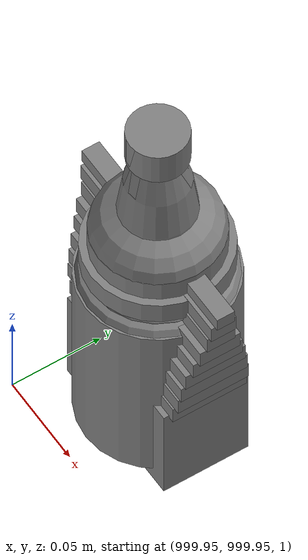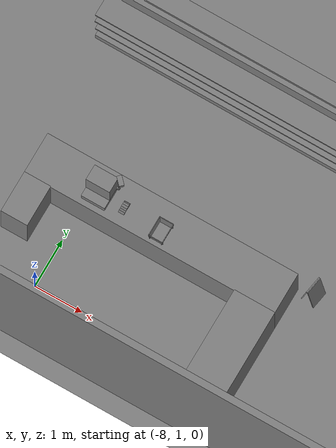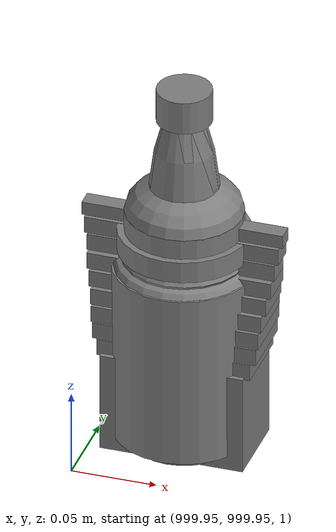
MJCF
<mujoco>
    <option gravity="0.000000000 0.000000000 -9.810000420" timestep="0.0166666" integrator="implicitfast" density="1.225" viscosity="1.8000001e-05" noslip_iterations="10" iterations="100" sdf_iterations="50">
        <flag multiccd="disable"/>
    </option>
    <size memory="1000M"/>
    <compiler coordinate="local"/>
    <worldbody>
        <light cutoff="30" pos="0 1 1" dir="0 -1 -2"/>
        <light cutoff="30" pos="0 -1 1" dir="0 1 -2"/>
        <body pos="0.000000000 0.000000000 0.000000000" euler="0.000000000 0.000000000 0.000000000" name="Interactive Objects_Interactive Objects"/>
        <body pos="1000.000000000 1000.000000000 1.000000000" euler="0.000000000 0.000000000 0.000000000" name="openloong_gripper_2f85_fix_base_usda_jar_01">
            <geom contype="1" conaffinity="1" density="1000" type="box" material="" rgba="0.500000000 0.500000000 0.500000000 1.000000000" solimp="0.899999976 0.949999988 0.001000000" friction="1.000000000 0.005000000 0.000100000" solref="0.020000000 1.000000000" margin="0" condim="3" group="0" pos="0.000000000 0.000000000 0.006158113" quat="1.000000000 0.000000000 0.000000000 0.000000000" size="0.020000000 0.020000000 0.005000000" name="openloong_gripper_2f85_fix_base_usda_geom_FF423E40_98BB_4650_86D8_D29294904E78"/>
            <geom contype="1" conaffinity="1" density="1000" type="cylinder" material="" rgba="0.500000000 0.500000000 0.500000000 1.000000000" solimp="0.899999976 0.949999988 0.001000000" friction="1.000000000 0.005000000 0.000100000" solref="0.020000000 1.000000000" margin="0" condim="3" group="0" pos="0.000000000 0.000000000 0.062744498" quat="1.000000000 0.000000000 0.000000000 0.000000000" size="0.041000001 0.052999999 1.000000000" name="openloong_gripper_2f85_fix_base_usda_geom_25061144_14CF_4C40_9A05_5D8598F43A68"/>
            <geom contype="1" conaffinity="1" density="1000" type="ellipsoid" material="" rgba="0.500000000 0.500000000 0.500000000 1.000000000" solimp="0.899999976 0.949999988 0.001000000" friction="1.000000000 0.005000000 0.000100000" solref="0.020000000 1.000000000" margin="0" condim="3" group="0" pos="0.000000000 0.000000000 0.122252703" quat="1.000000000 0.000000000 0.000000000 0.000000000" size="0.035999998 0.035999998 0.010000000" name="openloong_gripper_2f85_fix_base_usda_geom_2482B22A_793E_4E9A_A158_DD19B43CD848"/>
            <geom contype="1" conaffinity="1" density="1000" type="cylinder" material="" rgba="0.500000000 0.500000000 0.500000000 1.000000000" solimp="0.899999976 0.949999988 0.001000000" friction="1.000000000 0.005000000 0.000100000" solref="0.020000000 1.000000000" margin="0" condim="3" group="0" pos="0.000000000 0.000000000 0.015747190" quat="1.000000000 0.000000000 0.000000000 0.000000000" size="0.035000000 0.010000000 1.000000000" name="openloong_gripper_2f85_fix_base_usda_geom_654F59CA_C247_471A_85B2_DC2AB5531F33"/>
            <geom contype="1" conaffinity="1" density="1000" type="ellipsoid" material="" rgba="0.500000000 0.500000000 0.500000000 1.000000000" solimp="0.899999976 0.949999988 0.001000000" friction="1.000000000 0.005000000 0.000100000" solref="0.020000000 1.000000000" margin="0" condim="3" group="0" pos="0.000000000 0.000000000 0.115815401" quat="1.000000000 0.000000000 0.000000000 0.000000000" size="0.039999999 0.039999999 0.010000000" name="openloong_gripper_2f85_fix_base_usda_geom_AABC56B0_BCAC_4015_882E_B450C8500463"/>
            <geom contype="1" conaffinity="1" density="1000" type="cylinder" material="" rgba="0.500000000 0.500000000 0.500000000 1.000000000" solimp="0.899999976 0.949999988 0.001000000" friction="1.000000000 0.005000000 0.000100000" solref="0.020000000 1.000000000" margin="0" condim="3" group="0" pos="0.000000000 0.000000000 0.133183479" quat="1.000000000 0.000000000 0.000000000 0.000000000" size="0.037999999 0.006500000 1.000000000" name="openloong_gripper_2f85_fix_base_usda_geom_A47A47E8_B2F4_482C_8B9D_E79583EB03FD"/>
            <freejoint name="openloong_gripper_2f85_fix_base_usda_jar_01_joint"/>
            <site size="0.005000000 0.005000000 0.005000000" rgba="0.500000000 0.500000000 0.500000000 1.000000000" pos="0.000000000 0.000000000 0.000000000" quat="1.000000000 0.000000000 0.000000000 0.000000000" group="0" type="sphere" name="openloong_gripper_2f85_fix_base_usda_jar_01site"/>
        </body>
        <body pos="-2.338886499 6.006820202 1.663014650" euler="21.819223404 -50.746826172 -8.186965942" mocap="true" name="spotlight1_SpotLight"/>
        <body pos="1000.000000000 1000.000000000 1.000000000" euler="0.000000000 0.000000000 0.000000000" name="openloong_gripper_2f85_fix_base_usda_bottle_red">
            <geom contype="1" conaffinity="1" density="1000" type="ellipsoid" material="" rgba="0.500000000 0.500000000 0.500000000 1.000000000" solimp="0.899999976 0.949999988 0.001000000" friction="1.000000000 0.005000000 0.000100000" solref="0.020000000 1.000000000" margin="0" condim="3" group="0" pos="0.000000000 0.000000000 0.144284487" quat="1.000000000 0.000000000 0.000000000 0.000000000" size="0.021000000 0.021000000 0.079999998" name="openloong_gripper_2f85_fix_base_usda_geom_63AF62AF_C388_4828_A0B0_A6D5718D6A0A"/>
            <geom contype="1" conaffinity="1" density="1000" type="cylinder" material="" rgba="0.500000000 0.500000000 0.500000000 1.000000000" solimp="0.899999976 0.949999988 0.001000000" friction="1.000000000 0.005000000 0.000100000" solref="0.020000000 1.000000000" margin="0" condim="3" group="0" pos="0.000000000 0.000000000 0.220618963" quat="1.000000000 0.000000000 0.000000000 0.000000000" size="0.016000001 0.010000000 1.000000000" name="openloong_gripper_2f85_fix_base_usda_geom_447226DE_8104_4E49_8A1D_55F3418AF9B1"/>
            <geom contype="1" conaffinity="1" density="1000" type="ellipsoid" material="" rgba="0.500000000 0.500000000 0.500000000 1.000000000" solimp="0.899999976 0.949999988 0.001000000" friction="1.000000000 0.005000000 0.000100000" solref="0.020000000 1.000000000" margin="0" condim="3" group="0" pos="0.000000000 0.000000000 0.118945479" quat="1.000000000 0.000000000 0.000000000 0.000000000" size="0.030999999 0.030999999 0.029999999" name="openloong_gripper_2f85_fix_base_usda_geom_99A18CC9_EFB8_40A8_A204_31C019C01A4A"/>
            <geom contype="1" conaffinity="1" density="1000" type="box" material="" rgba="0.500000000 0.500000000 0.500000000 1.000000000" solimp="0.899999976 0.949999988 0.001000000" friction="1.000000000 0.005000000 0.000100000" solref="0.020000000 1.000000000" margin="0" condim="3" group="0" pos="0.000000000 0.000000000 0.002189159" quat="1.000000000 0.000000000 0.000000000 0.000000000" size="0.020000000 0.020000000 0.003000000" name="openloong_gripper_2f85_fix_base_usda_geom_A7FFE449_2F11_4A9E_9A61_9103060CCC62"/>
            <geom contype="1" conaffinity="1" density="1000" type="cylinder" material="" rgba="0.500000000 0.500000000 0.500000000 1.000000000" solimp="0.899999976 0.949999988 0.001000000" friction="1.000000000 0.005000000 0.000100000" solref="0.020000000 1.000000000" margin="0" condim="3" group="0" pos="0.000000000 -0.000366211 0.060884237" quat="1.000000000 0.000000000 0.000000000 0.000000000" size="0.030999999 0.057999998 1.000000000" name="openloong_gripper_2f85_fix_base_usda_geom_52FEB5C8_80B6_4A51_9F64_D9378D819242"/>
            <freejoint name="openloong_gripper_2f85_fix_base_usda_bottle_red_joint"/>
            <site size="0.005000000 0.005000000 0.005000000" rgba="0.500000000 0.500000000 0.500000000 1.000000000" pos="0.000000000 0.000000000 0.000000000" quat="0.999961913 0.008726535 0.000000000 0.000000000" group="0" type="sphere" name="openloong_gripper_2f85_fix_base_usda_bottle_redsite"/>
        </body>
        <body pos="1000.000000000 1000.000000000 1.000000000" euler="0.000000000 0.000000000 0.000000000" name="openloong_gripper_2f85_fix_base_usda_can">
            <geom contype="1" conaffinity="1" density="1000" type="cylinder" material="" rgba="0.500000000 0.500000000 0.500000000 1.000000000" solimp="0.899999976 0.949999988 0.001000000" friction="1.000000000 0.005000000 0.000100000" solref="0.020000000 1.000000000" margin="0" condim="3" group="0" pos="0.000000000 0.000000000 0.079676986" quat="1.000000000 0.000000000 0.000000000 0.000000000" size="0.034000002 0.071999997 1.000000000" name="openloong_gripper_2f85_fix_base_usda_geom_4E0E74AD_B626_4686_BEA6_51243EEE04AC"/>
            <geom contype="1" conaffinity="1" density="1000" type="ellipsoid" material="" rgba="0.500000000 0.500000000 0.500000000 1.000000000" solimp="0.899999976 0.949999988 0.001000000" friction="1.000000000 0.005000000 0.000100000" solref="0.020000000 1.000000000" margin="0" condim="3" group="0" pos="0.000000000 0.000000000 0.151854277" quat="1.000000000 0.000000000 0.000000000 0.000000000" size="0.034000002 0.034000002 0.020000000" name="openloong_gripper_2f85_fix_base_usda_geom_889C8543_F0DE_473E_AC52_0B77370B0394"/>
            <geom contype="1" conaffinity="1" density="1000" type="box" material="" rgba="0.500000000 0.500000000 0.500000000 1.000000000" solimp="0.899999976 0.949999988 0.001000000" friction="1.000000000 0.005000000 0.000100000" solref="0.020000000 1.000000000" margin="0" condim="3" group="0" pos="0.000000000 0.000000000 0.004777670" quat="1.000000000 0.000000000 0.000000000 0.000000000" size="0.020000000 0.020000000 0.005000000" name="openloong_gripper_2f85_fix_base_usda_geom_FCD75D46_8079_4B5F_A726_B796D7E76598"/>
            <freejoint name="openloong_gripper_2f85_fix_base_usda_can_joint"/>
            <site size="0.005000000 0.005000000 0.005000000" rgba="0.500000000 0.500000000 0.500000000 1.000000000" pos="0.000000000 0.000000000 0.000000000" quat="1.000000000 0.000000000 0.000000000 0.000000000" group="0" type="sphere" name="openloong_gripper_2f85_fix_base_usda_cansite"/>
        </body>
        <body pos="-1.937983155 6.597708702 1.714926481" euler="125.716316223 73.122749329 64.027175903" mocap="true" name="spotlight2_SpotLight"/>
        <body pos="1000.000000000 1000.000000000 1.000000000" euler="0.000000000 0.000000000 0.000000000" name="openloong_gripper_2f85_fix_base_usda_bottle_blue">
            <geom contype="1" conaffinity="1" density="1000" type="ellipsoid" material="" rgba="0.500000000 0.500000000 0.500000000 1.000000000" solimp="0.899999976 0.949999988 0.001000000" friction="1.000000000 0.005000000 0.000100000" solref="0.020000000 1.000000000" margin="0" condim="3" group="0" pos="0.000000000 0.000000000 0.118920922" quat="1.000000000 0.000000000 0.000000000 0.000000000" size="0.030999999 0.030999999 0.029999999" name="openloong_gripper_2f85_fix_base_usda_geom_5CD2B5BC_EC07_467D_92A0_53DC2A2E13B7"/>
            <geom contype="1" conaffinity="1" density="1000" type="box" material="" rgba="0.500000000 0.500000000 0.500000000 1.000000000" solimp="0.899999976 0.949999988 0.001000000" friction="1.000000000 0.005000000 0.000100000" solref="0.020000000 1.000000000" margin="0" condim="3" group="0" pos="0.000000000 0.000000000 0.002164602" quat="1.000000000 0.000000000 0.000000000 0.000000000" size="0.020000000 0.020000000 0.003000000" name="openloong_gripper_2f85_fix_base_usda_geom_B803A723_12AB_460D_BF11_735B7E937AD1"/>
            <geom contype="1" conaffinity="1" density="1000" type="cylinder" material="" rgba="0.500000000 0.500000000 0.500000000 1.000000000" solimp="0.899999976 0.949999988 0.001000000" friction="1.000000000 0.005000000 0.000100000" solref="0.020000000 1.000000000" margin="0" condim="3" group="0" pos="0.000000000 -0.000366211 0.060859680" quat="1.000000000 0.000000000 0.000000000 0.000000000" size="0.030999999 0.057999998 1.000000000" name="openloong_gripper_2f85_fix_base_usda_geom_37D2F925_1DFD_47BD_B648_FC977CD11042"/>
            <geom contype="1" conaffinity="1" density="1000" type="cylinder" material="" rgba="0.500000000 0.500000000 0.500000000 1.000000000" solimp="0.899999976 0.949999988 0.001000000" friction="1.000000000 0.005000000 0.000100000" solref="0.020000000 1.000000000" margin="0" condim="3" group="0" pos="0.000000000 0.000000000 0.220594406" quat="1.000000000 0.000000000 0.000000000 0.000000000" size="0.016000001 0.010000000 1.000000000" name="openloong_gripper_2f85_fix_base_usda_geom_B0D066BB_2EDE_41C8_972A_0C572F62A94B"/>
            <geom contype="1" conaffinity="1" density="1000" type="ellipsoid" material="" rgba="0.500000000 0.500000000 0.500000000 1.000000000" solimp="0.899999976 0.949999988 0.001000000" friction="1.000000000 0.005000000 0.000100000" solref="0.020000000 1.000000000" margin="0" condim="3" group="0" pos="0.000000000 0.000000000 0.144259930" quat="1.000000000 0.000000000 0.000000000 0.000000000" size="0.021000000 0.021000000 0.079999998" name="openloong_gripper_2f85_fix_base_usda_geom_0990E349_A44A_43B4_ADB2_D328AABC338E"/>
            <freejoint name="openloong_gripper_2f85_fix_base_usda_bottle_blue_joint"/>
            <site size="0.005000000 0.005000000 0.005000000" rgba="0.500000000 0.500000000 0.500000000 1.000000000" pos="0.000000000 0.000000000 0.000000000" quat="0.999961913 0.008726535 0.000000000 0.000000000" group="0" type="sphere" name="openloong_gripper_2f85_fix_base_usda_bottle_bluesite"/>
        </body>
        <body pos="-2.018316031 6.614463806 1.830832720" euler="106.417304993 -10.364501953 -51.066898346" mocap="true" name="spotlight5_SpotLight"/>
        <body pos="1000.000000000 1000.000000000 1.000000000" euler="0.000000000 0.000000000 0.000000000" name="openloong_gripper_2f85_fix_base_usda_salt">
            <geom contype="1" conaffinity="1" density="1000" type="box" material="" rgba="0.500000000 0.500000000 0.500000000 1.000000000" solimp="0.899999976 0.949999988 0.001000000" friction="1.000000000 0.005000000 0.000100000" solref="0.020000000 1.000000000" margin="0" condim="3" group="0" pos="0.000305176 0.000000000 0.084862232" quat="1.000000000 0.000000000 0.000000000 0.000000000" size="0.048999999 0.018999999 0.005000000" name="openloong_gripper_2f85_fix_base_usda_geom_63112AA9_9CAC_4A19_B49B_1F0A1035801A"/>
            <geom contype="1" conaffinity="1" density="1000" type="box" material="" rgba="0.500000000 0.500000000 0.500000000 1.000000000" solimp="0.899999976 0.949999988 0.001000000" friction="1.000000000 0.005000000 0.000100000" solref="0.020000000 1.000000000" margin="0" condim="3" group="0" pos="0.000305176 0.000000000 0.104564309" quat="1.000000000 0.000000000 0.000000000 0.000000000" size="0.052000001 0.014000000 0.005000000" name="openloong_gripper_2f85_fix_base_usda_geom_D8E47BDB_CBC0_413E_BD19_93DC5F79E5C3"/>
            <geom contype="1" conaffinity="1" density="1000" type="box" material="" rgba="0.500000000 0.500000000 0.500000000 1.000000000" solimp="0.899999976 0.949999988 0.001000000" friction="1.000000000 0.005000000 0.000100000" solref="0.020000000 1.000000000" margin="0" condim="3" group="0" pos="0.000305176 0.000000000 0.114487171" quat="1.000000000 0.000000000 0.000000000 0.000000000" size="0.054000001 0.011500000 0.005000000" name="openloong_gripper_2f85_fix_base_usda_geom_D513077F_C4F7_460E_8B80_D54CA56FD1A3"/>
            <geom contype="1" conaffinity="1" density="1000" type="box" material="" rgba="0.500000000 0.500000000 0.500000000 1.000000000" solimp="0.899999976 0.949999988 0.001000000" friction="1.000000000 0.005000000 0.000100000" solref="0.020000000 1.000000000" margin="0" condim="3" group="0" pos="0.000305176 0.000000000 0.075103164" quat="1.000000000 0.000000000 0.000000000 0.000000000" size="0.048000000 0.020000000 0.005000000" name="openloong_gripper_2f85_fix_base_usda_geom_BD67312E_18F4_402F_8543_BB75DBA83619"/>
            <geom contype="1" conaffinity="1" density="1000" type="box" material="" rgba="0.500000000 0.500000000 0.500000000 1.000000000" solimp="0.899999976 0.949999988 0.001000000" friction="1.000000000 0.005000000 0.000100000" solref="0.020000000 1.000000000" margin="0" condim="3" group="0" pos="0.000305176 0.000000000 0.134892464" quat="1.000000000 0.000000000 0.000000000 0.000000000" size="0.057000000 0.007000000 0.005000000" name="openloong_gripper_2f85_fix_base_usda_geom_2CC4A0F8_2247_4313_8E0C_B544F582E5DE"/>
            <geom contype="1" conaffinity="1" density="1000" type="box" material="" rgba="0.500000000 0.500000000 0.500000000 1.000000000" solimp="0.899999976 0.949999988 0.001000000" friction="1.000000000 0.005000000 0.000100000" solref="0.020000000 1.000000000" margin="0" condim="3" group="0" pos="0.000305176 0.000000000 0.094920278" quat="1.000000000 0.000000000 0.000000000 0.000000000" size="0.050000001 0.017000001 0.005000000" name="openloong_gripper_2f85_fix_base_usda_geom_4B77BCFA_93C0_4F42_A32F_BE462D0FE8B6"/>
            <geom contype="1" conaffinity="1" density="1000" type="box" material="" rgba="0.500000000 0.500000000 0.500000000 1.000000000" solimp="0.899999976 0.949999988 0.001000000" friction="1.000000000 0.005000000 0.000100000" solref="0.020000000 1.000000000" margin="0" condim="3" group="0" pos="0.000305176 0.000000000 0.065204859" quat="1.000000000 0.000000000 0.000000000 0.000000000" size="0.045000002 0.021000000 0.005000000" name="openloong_gripper_2f85_fix_base_usda_geom_4F3D7E28_5CCA_4BCA_AC07_B8ECDF846E1F"/>
            <geom contype="1" conaffinity="1" density="1000" type="box" material="" rgba="0.500000000 0.500000000 0.500000000 1.000000000" solimp="0.899999976 0.949999988 0.001000000" friction="1.000000000 0.005000000 0.000100000" solref="0.020000000 1.000000000" margin="0" condim="3" group="0" pos="0.000305176 0.000000000 0.144135714" quat="1.000000000 0.000000000 0.000000000 0.000000000" size="0.059000000 0.005000000 0.004000000" name="openloong_gripper_2f85_fix_base_usda_geom_1950766F_B26A_4A6F_B26B_14359CB525C1"/>
            <geom contype="1" conaffinity="1" density="1000" type="box" material="" rgba="0.500000000 0.500000000 0.500000000 1.000000000" solimp="0.899999976 0.949999988 0.001000000" friction="1.000000000 0.005000000 0.000100000" solref="0.020000000 1.000000000" margin="0" condim="3" group="0" pos="0.000000000 0.000000000 0.031593561" quat="1.000000000 0.000000000 0.000000000 0.000000000" size="0.041999999 0.024000000 0.029999999" name="openloong_gripper_2f85_fix_base_usda_geom_DFD8A317_9D6B_448C_9E6F_DD1FD62451A3"/>
            <geom contype="1" conaffinity="1" density="1000" type="box" material="" rgba="0.500000000 0.500000000 0.500000000 1.000000000" solimp="0.899999976 0.949999988 0.001000000" friction="1.000000000 0.005000000 0.000100000" solref="0.020000000 1.000000000" margin="0" condim="3" group="0" pos="0.000305176 0.000000000 0.124608755" quat="1.000000000 0.000000000 0.000000000 0.000000000" size="0.055000000 0.008000000 0.005000000" name="openloong_gripper_2f85_fix_base_usda_geom_EF18F2CA_B225_462D_BB02_27D73C73B807"/>
            <freejoint name="openloong_gripper_2f85_fix_base_usda_salt_joint"/>
            <site size="0.005000000 0.005000000 0.005000000" rgba="0.500000000 0.500000000 0.500000000 1.000000000" pos="0.000000000 0.000000000 0.000000000" quat="1.000000000 0.000000000 0.000000000 0.000000000" group="0" type="sphere" name="openloong_gripper_2f85_fix_base_usda_saltsite"/>
        </body>
        <body pos="0.000000000 0.000000000 0.000000000" euler="0.000000000 0.000000000 0.000000000" name=" Static Objects_ Static Objects">
            <geom contype="1" conaffinity="1" density="1000" type="box" material="" rgba="0.500000000 0.500000000 0.500000000 1.000000000" solimp="0.899999976 0.949999988 0.001000000" friction="1.000000000 0.005000000 0.000100000" solref="0.020000000 1.000000000" margin="0" condim="3" group="0" pos="-6.286010742 6.153595448 1.563861728" quat="0.707107067 0.000000000 0.000000000 0.707106471" size="0.529999971 3.134999990 0.025000000" name=" Static Objects_geom_157FE596_5930_474F_830C_69BEDA1226D1"/>
            <geom contype="1" conaffinity="1" density="1000" type="box" material="" rgba="0.500000000 0.500000000 0.500000000 1.000000000" solimp="0.899999976 0.949999988 0.001000000" friction="1.000000000 0.005000000 0.000100000" solref="0.020000000 1.000000000" margin="0" condim="3" group="0" pos="-3.101639986 6.150595188 1.018643856" quat="1.000000000 0.000000000 0.000000000 0.000000000" size="0.050000001 0.579999983 1.019999981" name=" Static Objects_geom_AEFF4C5F_23CC_4A7B_A6B0_13D4071C8FF3"/>
            <geom contype="1" conaffinity="1" density="1000" type="box" material="" rgba="0.500000000 0.500000000 0.500000000 1.000000000" solimp="0.899999976 0.949999988 0.001000000" friction="1.000000000 0.005000000 0.000100000" solref="0.020000000 1.000000000" margin="0" condim="3" group="0" pos="-2.825197220 6.153595448 1.563861728" quat="0.707107067 0.000000000 0.000000000 0.707106471" size="0.550000012 0.239999995 0.025000000" name=" Static Objects_geom_559FC648_4115_4555_9227_DF1CB55E1500"/>
            <geom contype="1" conaffinity="1" density="1000" type="box" material="" rgba="0.500000000 0.500000000 0.500000000 1.000000000" solimp="0.899999976 0.949999988 0.001000000" friction="1.000000000 0.005000000 0.000100000" solref="0.020000000 1.000000000" margin="0" condim="3" group="0" pos="-6.311686516 6.153595448 1.018643856" quat="0.707107067 0.000000000 0.000000000 0.707106471" size="0.050000001 3.150000095 1.019999981" name=" Static Objects_geom_9689A827_2C86_4D42_AFD7_552A3FF9366E"/>
            <geom contype="1" conaffinity="1" density="1000" type="box" material="" rgba="0.500000000 0.500000000 0.500000000 1.000000000" solimp="0.899999976 0.949999988 0.001000000" friction="1.000000000 0.005000000 0.000100000" solref="0.020000000 1.000000000" margin="0" condim="3" group="0" pos="-2.825197220 6.153595448 1.115278244" quat="0.707107067 0.000000000 0.000000000 0.707106471" size="0.550000012 0.239999995 0.025000000" name=" Static Objects_geom_A2DE7EAD_C8BF_496B_A4C1_0E58D0E1328C"/>
            <geom contype="1" conaffinity="1" density="1000" type="box" material="" rgba="0.500000000 0.500000000 0.500000000 1.000000000" solimp="0.899999976 0.949999988 0.001000000" friction="1.000000000 0.005000000 0.000100000" solref="0.020000000 1.000000000" margin="0" condim="3" group="0" pos="-6.293097973 6.153595448 1.114443064" quat="0.707107067 0.000000000 0.000000000 0.707106471" size="0.529999971 3.134999990 0.025000000" name=" Static Objects_geom_E53AFDAB_83E1_4252_A454_5DE96B1E14B7"/>
            <geom contype="1" conaffinity="1" density="1000" type="box" material="" rgba="0.500000000 0.500000000 0.500000000 1.000000000" solimp="0.899999976 0.949999988 0.001000000" friction="1.000000000 0.005000000 0.000100000" solref="0.020000000 1.000000000" margin="0" condim="3" group="0" pos="-2.825197220 6.153595448 0.629031777" quat="0.707107067 0.000000000 0.000000000 0.707106471" size="0.550000012 0.239999995 0.025000000" name=" Static Objects_geom_818940D5_2329_4DFC_9644_C845E827C60B"/>
            <geom contype="1" conaffinity="1" density="1000" type="box" material="" rgba="0.500000000 0.500000000 0.500000000 1.000000000" solimp="0.899999976 0.949999988 0.001000000" friction="1.000000000 0.005000000 0.000100000" solref="0.020000000 1.000000000" margin="0" condim="3" group="0" pos="-6.286010742 6.153595448 0.096129179" quat="0.707107067 0.000000000 0.000000000 0.707106471" size="0.529999971 3.134999990 0.098999999" name=" Static Objects_geom_2FA006D9_E5D4_4025_959B_57181868E208"/>
            <geom contype="1" conaffinity="1" density="1000" type="box" material="" rgba="0.500000000 0.500000000 0.500000000 1.000000000" solimp="0.899999976 0.949999988 0.001000000" friction="1.000000000 0.005000000 0.000100000" solref="0.020000000 1.000000000" margin="0" condim="3" group="0" pos="-2.825197220 6.153595448 0.097434282" quat="0.707107067 0.000000000 0.000000000 0.707106471" size="0.550000012 0.239999995 0.098999999" name=" Static Objects_geom_7F184EDC_3497_4A3F_B943_266EADACDCF9"/>
            <geom contype="1" conaffinity="1" density="1000" type="box" material="" rgba="0.500000000 0.500000000 0.500000000 1.000000000" solimp="0.899999976 0.949999988 0.001000000" friction="1.000000000 0.005000000 0.000100000" solref="0.020000000 1.000000000" margin="0" condim="3" group="0" pos="-6.286010742 6.153595448 0.629031777" quat="0.707107067 0.000000000 0.000000000 0.707106471" size="0.529999971 3.134999990 0.025000000" name=" Static Objects_geom_08098ABA_6E9E_4184_82E3_45C14389399E"/>
            <geom contype="1" conaffinity="1" density="1000" type="box" material="" rgba="0.500000000 0.500000000 0.500000000 1.000000000" solimp="0.899999976 0.949999988 0.001000000" friction="1.000000000 0.005000000 0.000100000" solref="0.020000000 1.000000000" margin="0" condim="3" group="0" pos="-6.000000000 20.159999847 2.000000000" quat="1.000000000 0.000000000 0.000000000 0.000000000" size="6.079999924 0.070000000 2.000000000" name=" Static Objects_geom_E2C9A736_FC27_4492_A9D1_A3F276D17C33"/>
            <geom contype="1" conaffinity="1" density="1000" type="box" material="" rgba="0.500000000 0.500000000 0.500000000 1.000000000" solimp="0.899999976 0.949999988 0.001000000" friction="1.000000000 0.005000000 0.000100000" solref="0.020000000 1.000000000" margin="0" condim="3" group="0" pos="-6.000000000 0.035000000 2.000000000" quat="1.000000000 0.000000000 0.000000000 0.000000000" size="6.079999924 0.070000000 2.000000000" name=" Static Objects_geom_DC168BA9_2A7F_40E4_9A00_EBAC6F7018DB"/>
            <geom contype="1" conaffinity="1" density="1000" type="box" material="" rgba="0.500000000 0.500000000 0.500000000 1.000000000" solimp="0.899999976 0.949999988 0.001000000" friction="1.000000000 0.005000000 0.000100000" solref="0.020000000 1.000000000" margin="0" condim="3" group="0" pos="0.000000000 10.000000000 2.000000000" quat="1.000000000 0.000000000 0.000000000 0.000000000" size="0.070000000 10.500000000 2.000000000" name=" Static Objects_geom_6DEE8A88_83CF_4EFD_80FB_9E3B0E638E53"/>
            <geom contype="1" conaffinity="1" density="1000" type="box" material="" rgba="0.500000000 0.500000000 0.500000000 1.000000000" solimp="0.899999976 0.949999988 0.001000000" friction="1.000000000 0.005000000 0.000100000" solref="0.020000000 1.000000000" margin="0" condim="3" group="0" pos="-12.050000191 10.000000000 2.000000000" quat="1.000000000 0.000000000 0.000000000 0.000000000" size="0.070000000 10.500000000 2.000000000" name=" Static Objects_geom_C72AC7A8_737A_4F8A_B7A7_61A8C41484EB"/>
            <geom contype="1" conaffinity="1" density="1000" type="plane" material="" rgba="0.500000000 0.500000000 0.500000000 1.000000000" solimp="0.899999976 0.949999988 0.001000000" friction="1.000000000 0.005000000 0.000100000" solref="0.020000000 1.000000000" margin="0" condim="3" group="0" pos="-6.000000000 10.399999619 0.000000000" quat="1.000000000 0.000000000 0.000000000 0.000000000" size="6.050000191 10.800000191 0.010000000" name=" Static Objects_geom_A308A373_4E2D_4342_A3AA_CDAB12EA3F55"/>
            <geom contype="1" conaffinity="1" density="1000" type="box" material="" rgba="0.500000000 0.500000000 0.500000000 1.000000000" solimp="0.899999976 0.949999988 0.001000000" friction="1.000000000 0.005000000 0.000100000" solref="0.020000000 1.000000000" margin="0" condim="3" group="0" pos="-8.830721855 2.096410990 0.549305558" quat="1.000000000 0.000000000 0.000000000 0.000000000" size="0.280000001 0.430000007 0.550000012" name=" Static Objects_geom_DE62594B_4E8C_4F4C_8FD9_6FC349F7ABFB"/>
            <geom contype="1" conaffinity="1" density="1000" type="box" material="" rgba="0.500000000 0.500000000 0.500000000 1.000000000" solimp="0.899999976 0.949999988 0.001000000" friction="1.000000000 0.005000000 0.000100000" solref="0.020000000 1.000000000" margin="0" condim="3" group="0" pos="-6.460197449 2.937205315 0.548931718" quat="1.000000000 0.000000000 0.000000000 0.000000000" size="2.650000095 0.430000007 0.550000012" name=" Static Objects_geom_F26029B7_A254_4D98_A6B1_6F0C8884D94F"/>
            <geom contype="1" conaffinity="1" density="1000" type="box" material="" rgba="0.500000000 0.500000000 0.500000000 1.000000000" solimp="0.899999976 0.949999988 0.001000000" friction="1.000000000 0.005000000 0.000100000" solref="0.020000000 1.000000000" margin="0" condim="3" group="0" pos="-4.240264893 1.327049494 0.549888909" quat="1.000000000 0.000000000 0.000000000 0.000000000" size="0.430000007 1.200000048 0.550000012" name=" Static Objects_geom_3C9CDA5C_869E_4546_B14D_B584AE2F2D9C"/>
            <geom contype="1" conaffinity="1" density="1000" type="box" material="" rgba="0.500000000 0.500000000 0.500000000 1.000000000" solimp="0.899999976 0.949999988 0.001000000" friction="1.000000000 0.005000000 0.000100000" solref="0.020000000 1.000000000" margin="0" condim="3" group="0" pos="-7.408766270 3.088089943 1.776644945" quat="0.928051054 0.000000000 0.000000000 0.372453064" size="0.050000001 0.100000001 0.050000001" name=" Static Objects_geom_56D55C6E_F6AA_4822_A5C6_28E73C2C61AB"/>
            <geom contype="1" conaffinity="1" density="1000" type="box" material="" rgba="0.500000000 0.500000000 0.500000000 1.000000000" solimp="0.899999976 0.949999988 0.001000000" friction="1.000000000 0.005000000 0.000100000" solref="0.020000000 1.000000000" margin="0" condim="3" group="0" pos="-7.437745571 3.067511320 1.289965630" quat="1.000000000 0.000000000 0.000000000 0.000000000" size="0.029999999 0.020000000 0.020000000" name=" Static Objects_geom_A516610C_3B30_4495_9C0C_5C920F211121"/>
            <geom contype="1" conaffinity="1" density="1000" type="box" material="" rgba="0.500000000 0.500000000 0.500000000 1.000000000" solimp="0.899999976 0.949999988 0.001000000" friction="1.000000000 0.005000000 0.000100000" solref="0.020000000 1.000000000" margin="0" condim="3" group="0" pos="-7.719123363 2.867671013 1.173410416" quat="1.000000000 0.000000000 0.000000000 0.000000000" size="0.250000000 0.250000000 0.079999998" name=" Static Objects_geom_93695E71_A9A4_433B_9379_6D0C47800891"/>
            <geom contype="1" conaffinity="1" density="1000" type="box" material="" rgba="0.500000000 0.500000000 0.500000000 1.000000000" solimp="0.899999976 0.949999988 0.001000000" friction="1.000000000 0.005000000 0.000100000" solref="0.020000000 1.000000000" margin="0" condim="3" group="0" pos="-7.719123363 2.958004713 1.530241251" quat="1.000000000 0.000000000 0.000000000 0.000000000" size="0.250000000 0.159999996 0.280000001" name=" Static Objects_geom_A66C5F02_33B3_47AC_BB5D_5DF301826248"/>
            <geom contype="1" conaffinity="1" density="1000" type="cylinder" material="" rgba="0.500000000 0.500000000 0.500000000 1.000000000" solimp="0.899999976 0.949999988 0.001000000" friction="1.000000000 0.005000000 0.000100000" solref="0.020000000 1.000000000" margin="0" condim="3" group="0" pos="-7.427312374 3.069516420 1.502544641" quat="0.928051054 0.000000000 0.000000000 0.372453064" size="0.015000000 0.230000004 0.100000001" name=" Static Objects_geom_25F31FBA_7977_483C_9A1E_CF74B8ACA994"/>
            <geom contype="1" conaffinity="1" density="1000" type="box" material="" rgba="0.500000000 0.500000000 0.500000000 1.000000000" solimp="0.899999976 0.949999988 0.001000000" friction="1.000000000 0.005000000 0.000100000" solref="0.020000000 1.000000000" margin="0" condim="3" group="0" pos="-9.058088303 6.434794426 1.209077358" quat="1.000000000 0.000000000 0.000000000 0.000000000" size="0.250000000 0.100000001 0.070000000" name=" Static Objects_geom_24F54262_F14E_493E_B4EF_03B2FE1C231C"/>
            <geom contype="1" conaffinity="1" density="1000" type="box" material="" rgba="0.500000000 0.500000000 0.500000000 1.000000000" solimp="0.899999976 0.949999988 0.001000000" friction="1.000000000 0.005000000 0.000100000" solref="0.020000000 1.000000000" margin="0" condim="3" group="0" pos="-5.611940861 6.318420410 0.350975692" quat="1.000000000 0.000000000 0.000000000 0.000000000" size="0.699999988 0.100000001 0.150000006" name=" Static Objects_geom_616279D0_4979_4662_82F8_6E937F0B5E93"/>
            <geom contype="1" conaffinity="1" density="1000" type="box" material="" rgba="0.500000000 0.500000000 0.500000000 1.000000000" solimp="0.899999976 0.949999988 0.001000000" friction="1.000000000 0.005000000 0.000100000" solref="0.020000000 1.000000000" margin="0" condim="3" group="0" pos="-9.237723351 6.464855671 1.209077358" quat="1.000000000 0.000000000 0.000000000 0.000000000" size="0.100000001 0.100000001 0.070000000" name=" Static Objects_geom_6DBE4FE4_E406_4DEA_AC66_43C22232194B"/>
            <geom contype="1" conaffinity="1" density="1000" type="box" material="" rgba="0.500000000 0.500000000 0.500000000 1.000000000" solimp="0.899999976 0.949999988 0.001000000" friction="1.000000000 0.005000000 0.000100000" solref="0.020000000 1.000000000" margin="0" condim="3" group="0" pos="-6.300771236 6.459744930 1.744376063" quat="1.000000000 0.000000000 0.000000000 0.000000000" size="3.000000000 0.200000003 0.150000006" name=" Static Objects_geom_7662C4F3_793C_46E0_8EEE_C0A70324C957"/>
            <geom contype="1" conaffinity="1" density="1000" type="box" material="" rgba="0.500000000 0.500000000 0.500000000 1.000000000" solimp="0.899999976 0.949999988 0.001000000" friction="1.000000000 0.005000000 0.000100000" solref="0.020000000 1.000000000" margin="0" condim="3" group="0" pos="-7.373087406 6.458900928 1.214329123" quat="1.000000000 0.000000000 0.000000000 0.000000000" size="0.250000000 0.200000003 0.075000003" name=" Static Objects_geom_1357F6F9_B552_42BF_8378_2F64077A1671"/>
            <geom contype="1" conaffinity="1" density="1000" type="box" material="" rgba="0.500000000 0.500000000 0.500000000 1.000000000" solimp="0.899999976 0.949999988 0.001000000" friction="1.000000000 0.005000000 0.000100000" solref="0.020000000 1.000000000" margin="0" condim="3" group="0" pos="-4.035642624 6.459744930 0.352518857" quat="1.000000000 0.000000000 0.000000000 0.000000000" size="0.800000012 0.200000003 0.150000006" name=" Static Objects_geom_83F03F18_B2AE_4B8E_841D_A7BCF996476A"/>
            <geom contype="1" conaffinity="1" density="1000" type="box" material="" rgba="0.500000000 0.500000000 0.500000000 1.000000000" solimp="0.899999976 0.949999988 0.001000000" friction="1.000000000 0.005000000 0.000100000" solref="0.020000000 1.000000000" margin="0" condim="3" group="0" pos="-3.907610416 6.318625927 0.800981164" quat="1.000000000 0.000000000 0.000000000 0.000000000" size="0.500000000 0.100000001 0.150000006" name=" Static Objects_geom_428C7F7D_726D_44BF_9EFE_2583204F36F3"/>
            <geom contype="1" conaffinity="1" density="1000" type="box" material="" rgba="0.500000000 0.500000000 0.500000000 1.000000000" solimp="0.899999976 0.949999988 0.001000000" friction="1.000000000 0.005000000 0.000100000" solref="0.020000000 1.000000000" margin="0" condim="3" group="0" pos="-6.098561764 6.327973843 1.292199373" quat="1.000000000 0.000000000 0.000000000 0.000000000" size="0.500000000 0.100000001 0.150000006" name=" Static Objects_geom_1A8E4C1C_6D05_4A0E_8684_9319DCA333E2"/>
            <geom contype="1" conaffinity="1" density="1000" type="box" material="" rgba="0.500000000 0.500000000 0.500000000 1.000000000" solimp="0.899999976 0.949999988 0.001000000" friction="1.000000000 0.005000000 0.000100000" solref="0.020000000 1.000000000" margin="0" condim="3" group="0" pos="-7.886891365 6.459744930 0.352518857" quat="1.000000000 0.000000000 0.000000000 0.000000000" size="1.500000000 0.200000003 0.150000006" name=" Static Objects_geom_7D52623A_D629_42E3_AB90_D858A1E59FB7"/>
            <geom contype="1" conaffinity="1" density="1000" type="box" material="" rgba="0.500000000 0.500000000 0.500000000 1.000000000" solimp="0.899999976 0.949999988 0.001000000" friction="1.000000000 0.005000000 0.000100000" solref="0.020000000 1.000000000" margin="0" condim="3" group="0" pos="-6.824534416 6.447464466 1.212718010" quat="1.000000000 0.000000000 0.000000000 0.000000000" size="0.100000001 0.100000001 0.075000003" name=" Static Objects_geom_C0CBA6C3_9D06_4134_9A71_1C78DBA0F910"/>
            <geom contype="1" conaffinity="1" density="1000" type="box" material="" rgba="0.500000000 0.500000000 0.500000000 1.000000000" solimp="0.899999976 0.949999988 0.001000000" friction="1.000000000 0.005000000 0.000100000" solref="0.020000000 1.000000000" margin="0" condim="3" group="0" pos="-4.407354832 6.459744930 1.292199373" quat="1.000000000 0.000000000 0.000000000 0.000000000" size="1.240000010 0.200000003 0.150000006" name=" Static Objects_geom_71FEB036_EAC4_4341_AA80_4AA72C2A93EF"/>
            <geom contype="1" conaffinity="1" density="1000" type="box" material="" rgba="0.500000000 0.500000000 0.500000000 1.000000000" solimp="0.899999976 0.949999988 0.001000000" friction="1.000000000 0.005000000 0.000100000" solref="0.020000000 1.000000000" margin="0" condim="3" group="0" pos="-6.751636982 6.459744930 0.800981164" quat="1.000000000 0.000000000 0.000000000 0.000000000" size="2.200000048 0.200000003 0.150000006" name=" Static Objects_geom_2BD5C591_A83D_48BE_A0F7_8F1700F27332"/>
            <geom contype="1" conaffinity="1" density="1000" type="box" material="" rgba="0.500000000 0.500000000 0.500000000 1.000000000" solimp="0.899999976 0.949999988 0.001000000" friction="1.000000000 0.005000000 0.000100000" solref="0.020000000 1.000000000" margin="0" condim="3" group="0" pos="-6.924745083 6.362090111 1.214329123" quat="1.000000000 0.000000000 0.000000000 0.000000000" size="0.200000003 0.100000001 0.075000003" name=" Static Objects_geom_BBE224EE_ADA4_46EF_84E1_DF0F531415B1"/>
            <geom contype="1" conaffinity="1" density="1000" type="box" material="" rgba="0.500000000 0.500000000 0.500000000 1.000000000" solimp="0.899999976 0.949999988 0.001000000" friction="1.000000000 0.005000000 0.000100000" solref="0.020000000 1.000000000" margin="0" condim="3" group="0" pos="-8.844120979 6.464855671 1.209077358" quat="1.000000000 0.000000000 0.000000000 0.000000000" size="0.100000001 0.100000001 0.070000000" name=" Static Objects_geom_87C4D3CA_9541_4215_8DBF_F44E41883788"/>
            <geom contype="1" conaffinity="1" density="1000" type="box" material="" rgba="0.500000000 0.500000000 0.500000000 1.000000000" solimp="0.899999976 0.949999988 0.001000000" friction="1.000000000 0.005000000 0.000100000" solref="0.020000000 1.000000000" margin="0" condim="3" group="0" pos="-3.157672644 6.136868477 1.348373055" quat="1.000000000 0.000000000 0.000000000 0.000000000" size="0.200000003 0.519999981 0.300000012" name=" Static Objects_geom_C436B44D_8D1F_4E93_B209_CC80EA82D713"/>
        </body>
        <body pos="-6.332345009 2.779978037 1.034067392" euler="0.000000000 0.000000000 0.000000000" name="openloong_gripper_2f85_fix_base_usda_basket">
            <geom contype="1" conaffinity="1" density="100000" type="box" material="" rgba="0.500000000 0.500000000 0.500000000 1.000000000" solimp="0.899999976 0.949999988 0.001000000" friction="1.000000000 0.899999976 0.000100000" solref="0.020000000 1.000000000" margin="0" condim="3" group="0" pos="-0.039724827 -0.188568115 0.167089701" quat="0.997537494 0.070135131 0.000000000 0.000000000" size="0.150000006 0.006000000 0.108000003" name="openloong_gripper_2f85_fix_base_usda_geom_9AEEE748_9E55_4BF6_AD7C_4A7FE165A892"/>
            <geom contype="1" conaffinity="1" density="100000" type="box" material="" rgba="0.500000000 0.500000000 0.500000000 1.000000000" solimp="0.899999976 0.949999988 0.001000000" friction="1.000000000 0.899999976 0.000100000" solref="0.020000000 1.000000000" margin="0" condim="3" group="0" pos="0.094372749 0.000000000 0.168361664" quat="0.706172049 0.036353335 0.036353379 0.706171215" size="0.200000003 0.006000000 0.108000003" name="openloong_gripper_2f85_fix_base_usda_geom_2C258E4D_B694_4391_9C80_B33A5FC41527"/>
            <geom contype="1" conaffinity="1" density="100000" type="box" material="" rgba="0.500000000 0.500000000 0.500000000 1.000000000" solimp="0.899999976 0.949999988 0.001000000" friction="1.000000000 0.899999976 0.000100000" solref="0.020000000 1.000000000" margin="0" condim="3" group="0" pos="-0.039724827 0.000000000 0.068126202" quat="1.000000000 0.000000000 0.000000000 0.000000000" size="0.129999995 0.174999997 0.006000000" name="openloong_gripper_2f85_fix_base_usda_geom_CBE953C3_4F06_4D4D_AB08_E55527E2591D"/>
            <geom contype="1" conaffinity="1" density="100000" type="box" material="" rgba="0.500000000 0.500000000 0.500000000 1.000000000" solimp="0.899999976 0.949999988 0.001000000" friction="1.000000000 0.899999976 0.000100000" solref="0.020000000 1.000000000" margin="0" condim="3" group="0" pos="-0.039724827 0.188377380 0.167089701" quat="0.997489929 -0.070808925 0.000000000 0.000000000" size="0.150000006 0.006000000 0.108000003" name="openloong_gripper_2f85_fix_base_usda_geom_FC38D983_3D5A_44CC_BAFB_22FB44B87B24"/>
            <geom contype="1" conaffinity="1" density="100000" type="box" material="" rgba="0.500000000 0.500000000 0.500000000 1.000000000" solimp="0.899999976 0.949999988 0.001000000" friction="1.000000000 0.899999976 0.000100000" solref="0.020000000 1.000000000" margin="0" condim="3" group="0" pos="-0.172339439 0.000000000 0.168361664" quat="0.706172407 -0.036353018 -0.036353093 0.706170976" size="0.200000003 0.006000000 0.108000003" name="openloong_gripper_2f85_fix_base_usda_geom_63C87D54_CFF7_4A43_97F9_AB27F8C691CA"/>
            <freejoint name="openloong_gripper_2f85_fix_base_usda_basket_joint"/>
            <site size="0.005000000 0.005000000 0.005000000" rgba="0.500000000 0.500000000 0.500000000 1.000000000" pos="0.000000000 0.000000000 0.000000000" quat="1.000000000 0.000000000 0.000000000 0.000000000" group="0" type="sphere" name="openloong_gripper_2f85_fix_base_usda_basketsite"/>
        </body>
        <body pos="-3.510578632 3.403555870 -0.000000100" euler="0.000000000 0.000000000 40.200675964" name="openloong_gripper_2f85_fix_base_usda_PZ">
            <geom contype="1" conaffinity="1" density="1000" type="box" material="" rgba="0.500000000 0.500000000 0.500000000 1.000000000" solimp="0.899999976 0.949999988 0.001000000" friction="1.000000000 0.005000000 0.000100000" solref="0.020000000 1.000000000" margin="0" condim="3" group="0" pos="-0.047453165 0.056484699 0.373715430" quat="0.934750080 0.077914521 0.028795123 0.345459938" size="0.180000007 0.010000000 0.379999995" name="openloong_gripper_2f85_fix_base_usda_geom_2AC785EA_014B_43A9_97DF_85E62726CD95"/>
            <geom contype="1" conaffinity="1" density="1000" type="box" material="" rgba="0.500000000 0.500000000 0.500000000 1.000000000" solimp="0.899999976 0.949999988 0.001000000" friction="1.000000000 0.005000000 0.000100000" solref="0.020000000 1.000000000" margin="0" condim="3" group="0" pos="0.047452450 -0.054376602 0.374072611" quat="0.934387863 -0.082143910 -0.030358355 0.345326364" size="0.180000007 0.010000000 0.379999995" name="openloong_gripper_2f85_fix_base_usda_geom_29F627DC_0C8E_4587_8D75_A964B6B0F3B0"/>
            <freejoint name="openloong_gripper_2f85_fix_base_usda_PZ"/>
        </body>
        <body pos="-7.168000221 2.823999882 1.227496982" euler="-0.283413976 0.056829724 -0.133293271" name="openloong_gripper_2f85_fix_base_usda_Pos">
            <geom contype="1" conaffinity="1" density="1000" type="box" material="" rgba="0.500000000 0.500000000 0.500000000 1.000000000" solimp="0.899999976 0.949999988 0.001000000" friction="1.000000000 0.005000000 0.000100000" solref="0.020000000 1.000000000" margin="0" condim="3" group="0" pos="-0.002278805 0.074524641 -0.004134059" quat="0.315989345 0.948763072 -0.000000000 0.000000000" size="0.059999999 0.013000000 0.035000000" name="openloong_gripper_2f85_fix_base_usda_geom_D6E3FE08_A293_4150_8382_F99FF5C1677B"/>
            <geom contype="1" conaffinity="1" density="1000" type="box" material="" rgba="0.500000000 0.500000000 0.500000000 1.000000000" solimp="0.899999976 0.949999988 0.001000000" friction="1.000000000 0.005000000 0.000100000" solref="0.020000000 1.000000000" margin="0" condim="3" group="0" pos="-0.002278805 0.078031301 0.008128285" quat="0.990447521 -0.137893379 -0.000000000 -0.000000000" size="0.059999999 0.010000000 0.035000000" name="openloong_gripper_2f85_fix_base_usda_geom_8B1B3C6C_98F5_4BE6_A93A_07735C172308"/>
            <geom contype="1" conaffinity="1" density="1000" type="box" material="" rgba="0.500000000 0.500000000 0.500000000 1.000000000" solimp="0.899999976 0.949999988 0.001000000" friction="1.000000000 0.005000000 0.000100000" solref="0.020000000 1.000000000" margin="0" condim="3" group="0" pos="-0.002278805 0.080785275 -0.002596974" quat="0.287325472 -0.957833409 0.000000000 -0.000000000" size="0.059999999 0.013000000 0.035000000" name="openloong_gripper_2f85_fix_base_usda_geom_88E016DB_E9B7_4011_AD4C_21CA40D0C6CA"/>
            <geom contype="1" conaffinity="1" density="1000" type="box" material="" rgba="0.500000000 0.500000000 0.500000000 1.000000000" solimp="0.899999976 0.949999988 0.001000000" friction="1.000000000 0.005000000 0.000100000" solref="0.020000000 1.000000000" margin="0" condim="3" group="0" pos="-0.002278805 -0.098804474 -0.020146966" quat="0.988851666 0.148906454 0.000000000 -0.000000000" size="0.059999999 0.022000000 0.020000000" name="openloong_gripper_2f85_fix_base_usda_geom_7ADDC03B_7271_46BF_B8E0_620FD4D54EB1"/>
            <geom contype="1" conaffinity="1" density="1000" type="box" material="" rgba="0.500000000 0.500000000 0.500000000 1.000000000" solimp="0.899999976 0.949999988 0.001000000" friction="1.000000000 0.005000000 0.000100000" solref="0.020000000 1.000000000" margin="0" condim="3" group="0" pos="-0.002279282 0.019920111 0.012102962" quat="0.995421767 0.095583342 -0.000000000 -0.000000000" size="0.059999999 0.025000000 0.026000001" name="openloong_gripper_2f85_fix_base_usda_geom_F316785A_01FF_4C7A_9508_FC2FAC8BDC62"/>
            <geom contype="1" conaffinity="1" density="1000" type="box" material="" rgba="0.500000000 0.500000000 0.500000000 1.000000000" solimp="0.899999976 0.949999988 0.001000000" friction="1.000000000 0.005000000 0.000100000" solref="0.020000000 1.000000000" margin="0" condim="3" group="0" pos="-0.002279282 0.005734444 -0.014276862" quat="0.999571741 -0.029275302 -0.000000000 -0.000000000" size="0.059999999 0.050000001 0.010000000" name="openloong_gripper_2f85_fix_base_usda_geom_8FAA2F21_E88A_4619_9AF4_3731BBFAB751"/>
            <geom contype="1" conaffinity="1" density="1000" type="box" material="" rgba="0.500000000 0.500000000 0.500000000 1.000000000" solimp="0.899999976 0.949999988 0.001000000" friction="1.000000000 0.005000000 0.000100000" solref="0.020000000 1.000000000" margin="0" condim="3" group="0" pos="-0.002278805 0.079460382 0.007771969" quat="0.922590554 -0.385781586 0.000000000 -0.000000000" size="0.059999999 0.010000000 0.035000000" name="openloong_gripper_2f85_fix_base_usda_geom_EAACFDEC_0E38_4C76_88EE_85260FA47D6A"/>
            <geom contype="1" conaffinity="1" density="1000" type="box" material="" rgba="0.500000000 0.500000000 0.500000000 1.000000000" solimp="0.899999976 0.949999988 0.001000000" friction="1.000000000 0.005000000 0.000100000" solref="0.020000000 1.000000000" margin="0" condim="3" group="0" pos="-0.002279282 0.081384182 -0.001320124" quat="0.590483785 -0.807049930 0.000000000 -0.000000000" size="0.059999999 0.013000000 0.035000000" name="openloong_gripper_2f85_fix_base_usda_geom_71C1F7B3_F0C3_4783_A627_6D22257D70E8"/>
            <geom contype="1" conaffinity="1" density="1000" type="box" material="" rgba="0.500000000 0.500000000 0.500000000 1.000000000" solimp="0.899999976 0.949999988 0.001000000" friction="1.000000000 0.005000000 0.000100000" solref="0.020000000 1.000000000" margin="0" condim="3" group="0" pos="-0.002278805 -0.059297800 -0.007972836" quat="0.988851666 0.148906454 0.000000000 -0.000000000" size="0.059999999 0.020000000 0.022000000" name="openloong_gripper_2f85_fix_base_usda_geom_67E0929A_E2DA_47DF_9A04_408B376883B3"/>
            <geom contype="1" conaffinity="1" density="1000" type="box" material="" rgba="0.500000000 0.500000000 0.500000000 1.000000000" solimp="0.899999976 0.949999988 0.001000000" friction="1.000000000 0.005000000 0.000100000" solref="0.020000000 1.000000000" margin="0" condim="3" group="0" pos="-0.002278805 0.076618671 -0.004656792" quat="0.004634961 0.999989629 -0.000000000 0.000000000" size="0.059999999 0.013000000 0.035000000" name="openloong_gripper_2f85_fix_base_usda_geom_E6716F10_BA7C_430E_9455_1C7621C5BEBE"/>
            <geom contype="1" conaffinity="1" density="1000" type="box" material="" rgba="0.500000000 0.500000000 0.500000000 1.000000000" solimp="0.899999976 0.949999988 0.001000000" friction="1.000000000 0.005000000 0.000100000" solref="0.020000000 1.000000000" margin="0" condim="3" group="0" pos="-0.002279282 -0.021952629 0.002960086" quat="0.991270423 0.131847665 -0.000000000 0.000000000" size="0.059999999 0.020000000 0.024000000" name="openloong_gripper_2f85_fix_base_usda_geom_1454A5ED_6C76_4ED1_A088_0CD9C7D9C95A"/>
            <geom contype="1" conaffinity="1" density="1000" type="box" material="" rgba="0.500000000 0.500000000 0.500000000 1.000000000" solimp="0.899999976 0.949999988 0.001000000" friction="1.000000000 0.005000000 0.000100000" solref="0.020000000 1.000000000" margin="0" condim="3" group="0" pos="-0.002278805 0.081418991 0.002587914" quat="0.803492308 -0.595315695 0.000000000 -0.000000000" size="0.059999999 0.013000000 0.035000000" name="openloong_gripper_2f85_fix_base_usda_geom_A04F0815_5913_4C53_AE88_8D9AD94F34FE"/>
            <geom contype="1" conaffinity="1" density="1000" type="box" material="" rgba="0.500000000 0.500000000 0.500000000 1.000000000" solimp="0.899999976 0.949999988 0.001000000" friction="1.000000000 0.005000000 0.000100000" solref="0.020000000 1.000000000" margin="0" condim="3" group="0" pos="-0.002278805 0.061115503 0.008545756" quat="0.999326169 0.036714450 0.000000000 -0.000000000" size="0.059999999 0.020000000 0.035000000" name="openloong_gripper_2f85_fix_base_usda_geom_EC004630_994B_4AB9_AF30_4DF3291F3685"/>
            <freejoint name="openloong_gripper_2f85_fix_base_usda_pos_scan"/>
        </body>
        <body pos="-2.436573029 6.404376507 0.137849092" euler="0.000000000 0.000000000 0.000000000" name="openloong_gripper_2f85_fix_base_usda_shoppingtrolley_01">
            <geom contype="1" conaffinity="1" density="1000" type="box" material="" rgba="0.500000000 0.500000000 0.500000000 1.000000000" solimp="0.899999976 0.949999988 0.001000000" friction="1.000000000 0.005000000 0.000100000" solref="0.020000000 1.000000000" margin="0" condim="3" group="0" pos="-0.107458733 0.238907143 0.911498845" quat="0.634576976 0.622505128 -0.330067992 -0.317575932" size="0.017999999 0.022499999 0.035999998" name="openloong_gripper_2f85_fix_base_usda_geom_12258030_2A5B_47CF_8B03_EA2506FAC8EE"/>
            <geom contype="1" conaffinity="1" density="1000" type="box" material="" rgba="0.500000000 0.500000000 0.500000000 1.000000000" solimp="0.899999976 0.949999988 0.001000000" friction="1.000000000 0.005000000 0.000100000" solref="0.020000000 1.000000000" margin="0" condim="3" group="0" pos="-0.126757339 -0.182533979 0.598989725" quat="0.996607184 0.055331606 -0.059003651 -0.015205891" size="0.013499999 0.287999988 0.053999998" name="openloong_gripper_2f85_fix_base_usda_geom_A29C4CA0_F3E3_4790_B689_6DFCA781E2F0"/>
            <geom contype="1" conaffinity="1" density="1000" type="box" material="" rgba="0.500000000 0.500000000 0.500000000 1.000000000" solimp="0.899999976 0.949999988 0.001000000" friction="1.000000000 0.005000000 0.000100000" solref="0.020000000 1.000000000" margin="0" condim="3" group="0" pos="-0.005004787 0.248085022 0.912686050" quat="1.000000000 0.000000000 0.000000000 0.000000000" size="0.107999995 0.022499999 0.022499999" name="openloong_gripper_2f85_fix_base_usda_geom_9FED7000_5713_4962_A6ED_90F91EBE5C2A"/>
            <geom contype="1" conaffinity="1" density="1000" type="box" material="" rgba="0.500000000 0.500000000 0.500000000 1.000000000" solimp="0.899999976 0.949999988 0.001000000" friction="1.000000000 0.005000000 0.000100000" solref="0.020000000 1.000000000" margin="0" condim="3" group="0" pos="-0.169898406 -0.043119621 0.915120542" quat="0.687021017 0.726584017 -0.005590606 -0.006832919" size="0.017999999 0.022499999 0.089999996" name="openloong_gripper_2f85_fix_base_usda_geom_DBBBA922_6B5E_4A67_A213_ECFA0117D934"/>
            <geom contype="1" conaffinity="1" density="1000" type="box" material="" rgba="0.500000000 0.500000000 0.500000000 1.000000000" solimp="0.899999976 0.949999988 0.001000000" friction="1.000000000 0.005000000 0.000100000" solref="0.020000000 1.000000000" margin="0" condim="3" group="0" pos="0.148195267 -0.199506566 0.782808602" quat="0.998808920 0.017156634 0.026950166 0.036880098" size="0.013499999 0.305999994 0.063000001" name="openloong_gripper_2f85_fix_base_usda_geom_0BFCFE44_9FBB_4D82_A1A2_CC64D1CEDD0D"/>
            <geom contype="1" conaffinity="1" density="1000" type="box" material="" rgba="0.500000000 0.500000000 0.500000000 1.000000000" solimp="0.899999976 0.949999988 0.001000000" friction="1.000000000 0.005000000 0.000100000" solref="0.020000000 1.000000000" margin="0" condim="3" group="0" pos="-0.142927840 -0.199506134 0.784674108" quat="0.998421252 0.016904408 -0.027109101 -0.046199299" size="0.013499999 0.305999994 0.063000001" name="openloong_gripper_2f85_fix_base_usda_geom_14ECB4D1_86F2_4D4B_B9D6_F1345F321D44"/>
            <geom contype="1" conaffinity="1" density="1000" type="box" material="" rgba="0.500000000 0.500000000 0.500000000 1.000000000" solimp="0.899999976 0.949999988 0.001000000" friction="1.000000000 0.005000000 0.000100000" solref="0.020000000 1.000000000" margin="0" condim="3" group="0" pos="-0.000004721 -0.174527690 0.560063601" quat="0.996704638 0.081116498 -0.000000004 0.000000000" size="0.126000002 0.287999988 0.009000000" name="openloong_gripper_2f85_fix_base_usda_geom_1512E577_FF98_440D_A915_33C57A8808BD"/>
            <geom contype="1" conaffinity="1" density="1000" type="box" material="" rgba="0.500000000 0.500000000 0.500000000 1.000000000" solimp="0.899999976 0.949999988 0.001000000" friction="1.000000000 0.005000000 0.000100000" solref="0.020000000 1.000000000" margin="0" condim="3" group="0" pos="-0.160832763 0.103427693 0.910528183" quat="0.711469591 0.699786782 -0.048386075 -0.042050660" size="0.017999999 0.022499999 0.071999997" name="openloong_gripper_2f85_fix_base_usda_geom_ECDECC28_4CEC_4A91_86CD_E4D7E49C1F40"/>
            <geom contype="1" conaffinity="1" density="1000" type="box" material="" rgba="0.500000000 0.500000000 0.500000000 1.000000000" solimp="0.899999976 0.949999988 0.001000000" friction="1.000000000 0.005000000 0.000100000" solref="0.020000000 1.000000000" margin="0" condim="3" group="0" pos="-0.169898406 -0.178061336 0.864131629" quat="0.916343808 -0.400392294 -0.000000045 0.000000030" size="0.017999999 0.022499999 0.089999996" name="openloong_gripper_2f85_fix_base_usda_geom_E5B5F362_0E1C_426F_8491_D4E6EF29A2A6"/>
            <geom contype="1" conaffinity="1" density="1000" type="box" material="" rgba="0.500000000 0.500000000 0.500000000 1.000000000" solimp="0.899999976 0.949999988 0.001000000" friction="1.000000000 0.005000000 0.000100000" solref="0.020000000 1.000000000" margin="0" condim="3" group="0" pos="-0.000006008 -0.484932661 0.670727849" quat="0.997585475 0.069449045 -0.000000004 -0.000000089" size="0.179999992 0.013499999 0.170999989" name="openloong_gripper_2f85_fix_base_usda_geom_3BC959C8_080E_474E_A144_0A444991D2B1"/>
            <geom contype="1" conaffinity="1" density="1000" type="box" material="" rgba="0.500000000 0.500000000 0.500000000 1.000000000" solimp="0.899999976 0.949999988 0.001000000" friction="1.000000000 0.005000000 0.000100000" solref="0.020000000 1.000000000" margin="0" condim="3" group="0" pos="0.134013891 0.200098798 0.912192523" quat="0.692574680 -0.680924535 -0.166899428 0.169783980" size="0.017999999 0.022499999 0.035999998" name="openloong_gripper_2f85_fix_base_usda_geom_27BB99E8_D127_47E3_ABE4_EEE2A1648BCF"/>
            <geom contype="1" conaffinity="1" density="1000" type="box" material="" rgba="0.500000000 0.500000000 0.500000000 1.000000000" solimp="0.899999976 0.949999988 0.001000000" friction="1.000000000 0.005000000 0.000100000" solref="0.020000000 1.000000000" margin="0" condim="3" group="0" pos="0.141839072 -0.191051379 0.702451229" quat="0.997147262 0.056065105 0.045779929 0.021407485" size="0.013499999 0.287999988 0.053999998" name="openloong_gripper_2f85_fix_base_usda_geom_A3A9875D_C4D1_4D41_95EF_50CB7B3CCEEB"/>
            <geom contype="1" conaffinity="1" density="1000" type="box" material="" rgba="0.500000000 0.500000000 0.500000000 1.000000000" solimp="0.899999976 0.949999988 0.001000000" friction="1.000000000 0.005000000 0.000100000" solref="0.020000000 1.000000000" margin="0" condim="3" group="0" pos="0.169898629 -0.178061336 0.864131629" quat="0.916343808 -0.400392294 -0.000000045 0.000000030" size="0.017999999 0.022499999 0.089999996" name="openloong_gripper_2f85_fix_base_usda_geom_32D5A1E5_1B89_4F12_AC9F_B0BA87601CA0"/>
            <geom contype="1" conaffinity="1" density="1000" type="box" material="" rgba="0.500000000 0.500000000 0.500000000 1.000000000" solimp="0.899999976 0.949999988 0.001000000" friction="1.000000000 0.005000000 0.000100000" solref="0.020000000 1.000000000" margin="0" condim="3" group="0" pos="-0.000005364 0.100332208 0.734785020" quat="0.999668717 0.025737956 -0.000000010 0.000000000" size="0.135000005 0.019800000 0.152999997" name="openloong_gripper_2f85_fix_base_usda_geom_CF06BC74_7560_4641_8AA1_66112EBAF4EC"/>
            <geom contype="1" conaffinity="1" density="1000" type="box" material="" rgba="0.500000000 0.500000000 0.500000000 1.000000000" solimp="0.899999976 0.949999988 0.001000000" friction="1.000000000 0.005000000 0.000100000" solref="0.020000000 1.000000000" margin="0" condim="3" group="0" pos="-0.012634277 -0.174527690 -0.088243507" quat="1.000000000 0.000000000 -0.000000004 0.000000000" size="0.135000005 0.287999988 0.044999998" name="openloong_gripper_2f85_fix_base_usda_geom_C1F90A6B_6429_46EA_968B_0AE8D630FB7F"/>
            <geom contype="1" conaffinity="1" density="1000" type="box" material="" rgba="0.500000000 0.500000000 0.500000000 1.000000000" solimp="0.899999976 0.949999988 0.001000000" friction="1.000000000 0.005000000 0.000100000" solref="0.020000000 1.000000000" margin="0" condim="3" group="0" pos="0.131482959 -0.182533979 0.598989725" quat="0.996607125 0.055331629 0.059003670 0.015205893" size="0.013499999 0.287999988 0.053999998" name="openloong_gripper_2f85_fix_base_usda_geom_CCD2EAEF_476A_4EFB_8C34_0AF2142C3EDE"/>
            <geom contype="1" conaffinity="1" density="1000" type="box" material="" rgba="0.500000000 0.500000000 0.500000000 1.000000000" solimp="0.899999976 0.949999988 0.001000000" friction="1.000000000 0.005000000 0.000100000" solref="0.020000000 1.000000000" margin="0" condim="3" group="0" pos="0.103667587 0.233050480 0.912927270" quat="0.634205043 -0.622199059 -0.324503720 0.324576139" size="0.017999999 0.022499999 0.035999998" name="openloong_gripper_2f85_fix_base_usda_geom_F9595928_1259_42DE_9B8B_5B3769D651F6"/>
            <geom contype="1" conaffinity="1" density="1000" type="box" material="" rgba="0.500000000 0.500000000 0.500000000 1.000000000" solimp="0.899999976 0.949999988 0.001000000" friction="1.000000000 0.005000000 0.000100000" solref="0.020000000 1.000000000" margin="0" condim="3" group="0" pos="-0.134013891 0.200098798 0.912192523" quat="0.694057047 0.679413557 -0.172947660 -0.163618833" size="0.017999999 0.022499999 0.035999998" name="openloong_gripper_2f85_fix_base_usda_geom_C3F6FAB1_EF49_4B24_9808_D87D9B03A98B"/>
            <geom contype="1" conaffinity="1" density="1000" type="box" material="" rgba="0.500000000 0.500000000 0.500000000 1.000000000" solimp="0.899999976 0.949999988 0.001000000" friction="1.000000000 0.005000000 0.000100000" solref="0.020000000 1.000000000" margin="0" condim="3" group="0" pos="-0.135714188 -0.191051379 0.694841146" quat="0.997147322 0.056064609 -0.045779683 -0.021407485" size="0.013499999 0.287999988 0.053999998" name="openloong_gripper_2f85_fix_base_usda_geom_495FF21A_FBD2_456F_A28E_BA075D45F8E3"/>
            <geom contype="1" conaffinity="1" density="1000" type="box" material="" rgba="0.500000000 0.500000000 0.500000000 1.000000000" solimp="0.899999976 0.949999988 0.001000000" friction="1.000000000 0.005000000 0.000100000" solref="0.020000000 1.000000000" margin="0" condim="3" group="0" pos="0.169898629 -0.043119621 0.915120542" quat="0.687029123 -0.726576388 -0.006509603 0.005963952" size="0.017999999 0.022499999 0.089999996" name="openloong_gripper_2f85_fix_base_usda_geom_112417D9_F797_4295_ABE3_D84D40E70A42"/>
            <geom contype="1" conaffinity="1" density="1000" type="box" material="" rgba="0.500000000 0.500000000 0.500000000 1.000000000" solimp="0.899999976 0.949999988 0.001000000" friction="1.000000000 0.005000000 0.000100000" solref="0.020000000 1.000000000" margin="0" condim="3" group="0" pos="0.160832971 0.103427693 0.910528183" quat="0.711112797 -0.700149298 -0.042821646 0.047705106" size="0.017999999 0.022499999 0.071999997" name="openloong_gripper_2f85_fix_base_usda_geom_0094CE2F_369B_45CB_BFDD_32B613FE9AAC"/>
            <freejoint name="openloong_gripper_2f85_fix_base_usda_shoppingtrolley_01_joint"/>
            <site size="0.005000000 0.005000000 0.005000000" rgba="0.500000000 0.500000000 0.500000000 1.000000000" pos="0.000000000 0.000000000 0.000000000" quat="1.000000000 0.000000000 0.000000000 0.000000000" group="0" type="sphere" name="openloong_gripper_2f85_fix_base_usda_shoppingtrolley_01"/>
        </body>
        <body pos="-2.162922621 6.180304527 -0.123990871" euler="0.000000000 0.000000000 180.000000000" mocap="true" name="openloong_gripper_2f85_fix_base_usda_leftHandMocap"/>
        <body pos="-2.162922621 6.180304527 -0.123990871" euler="0.000000000 0.000000000 180.000000000" mocap="true" name="openloong_gripper_2f85_fix_base_usda_rightHandMocap"/>
        <body pos="-2.162922621 6.180304527 1.076009154" euler="0.000000000 0.000000000 180.000000000" name="openloong_gripper_2f85_fix_base_usda_base_link">
            <geom contype="1" conaffinity="1" density="1000" type="mesh" material="" rgba="0.783999979 0.783999979 0.783999979 1.000000000" solimp="0.899999976 0.949999988 0.001000000" friction="1.000000000 0.005000000 0.000100000" solref="0.020000000 1.000000000" margin="0" condim="3" group="3" mesh="base_link" pos="0.000000000 0.000000000 0.000000000" quat="1.000000000 0.000000000 0.000000000 0.000000000" size="1.000000000 1.000000000 1.000000000" name="openloong_gripper_2f85_fix_base_usda__geom_7_3494EBEE_02A0_4849_82A3_04586F1E8510"/>
            <site size="0.005000000 0.005000000 0.005000000" rgba="0.500000000 0.500000000 0.500000000 1.000000000" pos="0.000000000 0.000000000 0.000000000" quat="1.000000000 0.000000000 0.000000000 0.000000000" group="0" type="sphere" name="openloong_gripper_2f85_fix_base_usda_imu"/>
            <inertial mass="22.447001" pos="-0.005664100 -0.001336700 0.238289997" diaginertia="0.374352545 0.277180195 0.220617250" quat="0.999247074 0.035235517 -0.015086859 0.006023135"/>
            <body pos="0.000000000 0.000000000 0.300000072" euler="0.000000000 0.000000000 0.000000000" name="openloong_gripper_2f85_fix_base_usda_dummy_body">
                <geom contype="1" conaffinity="1" density="1000" type="sphere" material="" rgba="0.783999979 0.783999979 0.783999979 1.000000000" solimp="0.899999976 0.949999988 0.001000000" friction="1.000000000 0.005000000 0.000100000" solref="0.020000000 1.000000000" margin="0" condim="3" group="3" pos="0.000000000 0.000000000 0.000000000" quat="1.000000000 0.000000000 0.000000000 0.000000000" size="0.010000000 0.000000000 0.000000000" name="openloong_gripper_2f85_fix_base_usda__geom_8_FD1558BC_FB54_4C70_BACF_B49D44F53681"/>
                <joint armature="0.0099999998" stiffness="0" damping="0.1" axis="0.000000 0.000000 1.000000" type="hinge" name="openloong_gripper_2f85_fix_base_usda_dummy_joint"/>
                <site size="0.010000000 0.005000000 0.005000000" rgba="0.500000000 0.500000000 0.500000000 1.000000000" pos="0.000000000 0.000000000 0.000000000" quat="1.000000000 0.000000000 0.000000000 0.000000000" group="3" type="sphere" name="openloong_gripper_2f85_fix_base_usda_dummy_site"/>
            </body>
            <body pos="0.009000063 0.000000000 0.406399965" euler="0.000000000 0.000000000 0.000000000" name="openloong_gripper_2f85_fix_base_usda_Link_head_yaw">
                <geom contype="1" conaffinity="1" density="1000" type="mesh" material="" rgba="0.783999979 0.783999979 0.783999979 1.000000000" solimp="0.899999976 0.949999988 0.001000000" friction="1.000000000 0.005000000 0.000100000" solref="0.020000000 1.000000000" margin="0" condim="3" group="3" mesh="Link_head_yaw" pos="0.000000000 0.000000000 0.000000000" quat="1.000000000 0.000000000 0.000000000 0.000000000" size="1.000000000 1.000000000 1.000000000" name="openloong_gripper_2f85_fix_base_usda__geom_10_BE8D6CCD_8D2C_4C4D_BAFA_0137BD0B91B8"/>
                <inertial mass="0.84249002" pos="0.000000000 -0.002081400 0.044801001" diaginertia="0.000700588 0.000629000 0.000553812" quat="0.706933022 -0.015675601 0.015677100 0.706933022"/>
                <body pos="0.000000000 -0.034599781 0.048499942" euler="0.000000000 0.000000000 0.000000000" name="openloong_gripper_2f85_fix_base_usda_Link_head_pitch">
                    <geom contype="1" conaffinity="1" density="1000" type="mesh" material="" rgba="0.783999979 0.783999979 0.783999979 1.000000000" solimp="0.899999976 0.949999988 0.001000000" friction="1.000000000 0.005000000 0.000100000" solref="0.020000000 1.000000000" margin="0" condim="3" group="3" mesh="Link_head_pitch" pos="0.000000000 0.000000000 0.000000000" quat="1.000000000 0.000000000 0.000000000 0.000000000" size="1.000000000 1.000000000 1.000000000" name="openloong_gripper_2f85_fix_base_usda__geom_12_EAC306B2_5904_406E_A65C_1123FFE3F916"/>
                    <inertial mass="1.3943" pos="0.020569000 0.033004001 0.125000000" diaginertia="0.006381400 0.006289940 0.004481460" quat="0.973390222 0.008406822 0.228157058 0.019624906"/>
                    <body pos="0.000000000 0.030000210 0.000000000" euler="0.000000000 0.000000000 0.000000000" name="openloong_gripper_2f85_fix_base_usda_neck_center_body">
                        <site size="0.010000000 0.005000000 0.005000000" rgba="0.500000000 0.500000000 0.500000000 1.000000000" pos="0.000000000 0.000000000 0.000000000" quat="1.000000000 0.000000000 0.000000000 0.000000000" group="3" type="sphere" name="openloong_gripper_2f85_fix_base_usda_neck_center_site"/>
                        <body pos="0.019999981 0.000000000 0.149999976" euler="-0.000002229 39.998176575 -90.000205994" name="openloong_gripper_2f85_fix_base_usda_camera_head">
                            <site size="0.010000000 0.005000000 0.005000000" rgba="0.500000000 0.500000000 0.500000000 1.000000000" pos="0.000000000 0.000000000 0.000000000" quat="1.000000000 0.000000000 0.000000000 0.000000000" group="3" type="sphere" name="openloong_gripper_2f85_fix_base_usda_camera_head_site"/>
                        </body>
                    </body>
                </body>
            </body>
            <body pos="0.003999949 -0.161600113 0.392199993" euler="0.000000000 0.000000000 0.000000000" name="openloong_gripper_2f85_fix_base_usda_Link_arm_r_01">
                <geom contype="1" conaffinity="1" density="1000" type="mesh" material="" rgba="0.783999979 0.783999979 0.783999979 1.000000000" solimp="0.899999976 0.949999988 0.001000000" friction="1.000000000 0.005000000 0.000100000" solref="0.020000000 1.000000000" margin="0" condim="3" group="3" mesh="Link_arm_r_01" pos="0.000000000 0.000000000 0.000000000" quat="1.000000000 0.000000000 0.000000000 0.000000000" size="1.000000000 1.000000000 1.000000000" name="openloong_gripper_2f85_fix_base_usda__geom_14_00CD9ABB_904E_48DA_BEC6_80F995BEA2AA"/>
                <joint armature="0.0099999998" stiffness="0" damping="1" axis="0.000000 -1.000000 0.000000" limited="true" range="-170.000015259 170.000015259" type="hinge" name="openloong_gripper_2f85_fix_base_usda_J_arm_r_01"/>
                <inertial mass="0.75641" pos="0.004494600 -0.038293999 -0.000001874" diaginertia="0.000842990 0.000803050 0.000587120" quat="-0.000163502 0.707098067 0.000812463 0.707115054"/>
                <body pos="-0.042000055 -0.040999889 0.000000000" euler="0.000000000 0.000000000 0.000000000" name="openloong_gripper_2f85_fix_base_usda_Link_arm_r_02">
                    <geom contype="1" conaffinity="1" density="1000" type="mesh" material="" rgba="0.783999979 0.783999979 0.783999979 1.000000000" solimp="0.899999976 0.949999988 0.001000000" friction="1.000000000 0.005000000 0.000100000" solref="0.020000000 1.000000000" margin="0" condim="3" group="3" mesh="Link_arm_r_02" pos="0.000000000 0.000000000 0.000000000" quat="1.000000000 0.000000000 0.000000000 0.000000000" size="1.000000000 1.000000000 1.000000000" name="openloong_gripper_2f85_fix_base_usda__geom_16_C2A3BAFF_922F_41B7_BA8B_1DFFE580F5FF"/>
                    <joint armature="0.0099999998" stiffness="0" damping="1" axis="-1.000000 0.000000 0.000000" limited="true" range="-105.000244141 105.000244141" type="hinge" name="openloong_gripper_2f85_fix_base_usda_J_arm_r_02"/>
                    <inertial mass="0.98500001" pos="0.041999999 -0.067430697 0.000000000" diaginertia="0.002262690 0.001730990 0.001154020" quat="0.500000000 0.500000000 -0.500000000 0.500000000"/>
                    <body pos="0.042000055 -0.122600079 0.000000000" euler="0.000000000 0.000000000 0.000000000" name="openloong_gripper_2f85_fix_base_usda_Link_arm_r_03">
                        <geom contype="1" conaffinity="1" density="1000" type="mesh" material="" rgba="0.783999979 0.783999979 0.783999979 1.000000000" solimp="0.899999976 0.949999988 0.001000000" friction="1.000000000 0.005000000 0.000100000" solref="0.020000000 1.000000000" margin="0" condim="3" group="3" mesh="Link_arm_r_03" pos="0.000000000 0.000000000 0.000000000" quat="1.000000000 0.000000000 0.000000000 0.000000000" size="1.000000000 1.000000000 1.000000000" name="openloong_gripper_2f85_fix_base_usda__geom_18_2E3870A4_CE57_4F35_9F4F_0D41AF782B16"/>
                        <joint armature="0.0099999998" stiffness="0" damping="1" axis="0.000000 -1.000000 0.000000" limited="true" range="-170.000015259 170.000015259" type="hinge" name="openloong_gripper_2f85_fix_base_usda_J_arm_r_03"/>
                        <inertial mass="0.95899999" pos="-0.001413580 -0.164663002 0.020757901" diaginertia="0.002101340 0.002064590 0.000754802" quat="0.560480952 0.454391927 -0.443732947 0.531497955"/>
                        <body pos="0.035300016 -0.177400112 0.024000049" euler="0.000000000 0.000000000 0.000000000" name="openloong_gripper_2f85_fix_base_usda_Link_arm_r_04">
                            <geom contype="1" conaffinity="1" density="1000" type="mesh" material="" rgba="0.783999979 0.783999979 0.783999979 1.000000000" solimp="0.899999976 0.949999988 0.001000000" friction="1.000000000 0.005000000 0.000100000" solref="0.020000000 1.000000000" margin="0" condim="3" group="3" mesh="Link_arm_r_04" pos="0.000000000 0.000000000 0.000000000" quat="1.000000000 0.000000000 0.000000000 0.000000000" size="1.000000000 1.000000000 1.000000000" name="openloong_gripper_2f85_fix_base_usda__geom_20_4985B824_5293_4D36_B675_008D7AB9BD7F"/>
                            <joint armature="0.0099999998" stiffness="0" damping="1" axis="-1.000000 0.000000 0.000000" limited="true" range="0.000000000 170.000015259" type="hinge" name="openloong_gripper_2f85_fix_base_usda_J_arm_r_04"/>
                            <inertial mass="0.60000002" pos="-0.038727000 -0.060766999 -0.021003000" diaginertia="0.001092610 0.000712422 0.000645102" quat="0.327701002 0.632602990 -0.467366993 0.523443997"/>
                            <body pos="-0.035300016 -0.103499889 -0.024000049" euler="0.000000000 0.000000000 0.000000000" name="openloong_gripper_2f85_fix_base_usda_Link_arm_r_05">
                                <geom contype="1" conaffinity="1" density="1000" type="mesh" material="" rgba="0.783999979 0.783999979 0.783999979 1.000000000" solimp="0.899999976 0.949999988 0.001000000" friction="1.000000000 0.005000000 0.000100000" solref="0.020000000 1.000000000" margin="0" condim="3" group="3" mesh="Link_arm_r_05" pos="0.000000000 0.000000000 0.000000000" quat="1.000000000 0.000000000 0.000000000 0.000000000" size="1.000000000 1.000000000 1.000000000" name="openloong_gripper_2f85_fix_base_usda__geom_22_52852E8A_6CD2_4C9A_8014_32456A98D8B2"/>
                                <joint armature="0.0099999998" stiffness="0" damping="1" axis="0.000000 -1.000000 0.000000" limited="true" range="-170.000015259 170.000015259" type="hinge" name="openloong_gripper_2f85_fix_base_usda_J_arm_r_05"/>
                                <inertial mass="0.68976003" pos="0.000032712 -0.068658002 -0.000111780" diaginertia="0.002522510 0.002411100 0.000448695" quat="0.707660973 0.706543028 -0.002603360 0.002470550"/>
                                <body pos="-0.026499987 -0.196499825 0.000000000" euler="0.000000000 0.000000000 0.000000000" name="openloong_gripper_2f85_fix_base_usda_Link_arm_r_06">
                                    <geom contype="1" conaffinity="1" density="1000" type="mesh" material="" rgba="0.783999979 0.783999979 0.783999979 1.000000000" solimp="0.899999976 0.949999988 0.001000000" friction="1.000000000 0.005000000 0.000100000" solref="0.020000000 1.000000000" margin="0" condim="3" group="3" mesh="Link_arm_r_06" pos="0.000000000 0.000000000 0.000000000" quat="1.000000000 0.000000000 0.000000000 0.000000000" size="1.000000000 1.000000000 1.000000000" name="openloong_gripper_2f85_fix_base_usda__geom_24_BE54F73F_42EC_4298_80AC_E42E535420AA"/>
                                    <joint armature="0.0099999998" stiffness="0" damping="1" axis="1.000000 0.000000 0.000000" limited="true" range="-105.000244141 105.000244141" type="hinge" name="openloong_gripper_2f85_fix_base_usda_J_arm_r_06"/>
                                    <inertial mass="0.28" pos="0.026078001 -0.000000896 0.001663700" diaginertia="0.000156930 0.000145601 0.000104979" quat="0.707080841 0.001851080 0.001883810 0.707127810"/>
                                    <body pos="0.026499987 0.000000000 0.031800032" euler="0.000000000 0.000000000 0.000000000" name="openloong_gripper_2f85_fix_base_usda_Link_arm_r_07">
                                        <geom contype="1" conaffinity="1" density="1000" type="mesh" material="" rgba="0.783999979 0.783999979 0.783999979 1.000000000" solimp="0.899999976 0.949999988 0.001000000" friction="1.000000000 0.005000000 0.000100000" solref="0.020000000 1.000000000" margin="0" condim="3" group="3" mesh="Link_arm_r_07" pos="0.000000000 0.000000000 0.000000000" quat="1.000000000 0.000000000 0.000000000 0.000000000" size="1.000000000 1.000000000 1.000000000" name="openloong_gripper_2f85_fix_base_usda__geom_26_A5E33109_05D7_4373_9026_FD9D8CCAB888"/>
                                        <joint armature="0.0099999998" stiffness="0" damping="1" axis="0.000000 0.000000 1.000000" limited="true" range="-60.000133514 60.000133514" type="hinge" name="openloong_gripper_2f85_fix_base_usda_J_arm_r_07"/>
                                        <inertial mass="0.61353999" pos="-0.007859000 -0.158170000 -0.027736001" diaginertia="0.003037610 0.002570910 0.000729379" quat="0.427542925 0.443532884 -0.553093910 0.560867906"/>
                                        <body pos="0.000000000 0.287000179 -0.269999981" euler="150.000350952 0.000000000 0.000000000" name="openloong_gripper_2f85_fix_base_usda_camera_wrist_r">
                                            <site size="0.010000000 0.005000000 0.005000000" rgba="0.500000000 0.500000000 0.500000000 1.000000000" pos="0.000000000 0.000000000 0.000000000" quat="1.000000000 0.000000000 0.000000000 0.000000000" group="3" type="sphere" name="openloong_gripper_2f85_fix_base_usda_camera_wrist_r_site"/>
                                        </body>
                                        <body pos="0.000000000 -0.219999790 -0.032999992" euler="0.000000000 0.000000000 179.999969482" name="openloong_gripper_2f85_fix_base_usda_ee_center_body_r">
                                            <site size="0.010000000 0.005000000 0.005000000" rgba="0.500000000 0.500000000 0.500000000 1.000000000" pos="0.000000000 0.000000000 0.000000000" quat="1.000000000 0.000000000 0.000000000 0.000000000" group="3" type="sphere" name="openloong_gripper_2f85_fix_base_usda_ee_center_site_r"/>
                                        </body>
                                        <body pos="0.000000000 -0.065999985 -0.031000018" euler="89.999984741 0.000000000 180.000000000" name="openloong_gripper_2f85_fix_base_usda_zbr_base_link">
                                            <geom contype="1" conaffinity="1" density="1000" type="mesh" material="" rgba="0.783999979 0.783999979 0.783999979 1.000000000" solimp="0.899999976 0.949999988 0.001000000" friction="1.000000000 0.005000000 0.000100000" solref="0.020000000 1.000000000" margin="0" condim="3" group="3" mesh="base" pos="0.000000000 0.000000000 0.000000000" quat="1.000000000 0.000000000 0.000000000 0.000000000" size="1.000000238 1.000000238 1.000000238" name="openloong_gripper_2f85_fix_base_usda__geom_30_EB655679_DF60_44B2_A38A_1001448196F6"/>
                                            <inertial mass="0.77744102" pos="0.000000000 -0.000027039 0.035467502" diaginertia="0.000260285 0.000225381 0.000152708" quat="0.999998808 -0.001528488 0.000000000 0.000000000"/>
                                            <body pos="-0.030601032 0.004750133 0.065703884" euler="-89.999977112 0.000000000 0.000000000" name="openloong_gripper_2f85_fix_base_usda_r_left_driver">
                                                <geom contype="1" conaffinity="1" density="1000" type="mesh" material="" rgba="0.783999979 0.783999979 0.783999979 1.000000000" solimp="0.899999976 0.949999988 0.001000000" friction="1.000000000 0.005000000 0.000100000" solref="0.020000000 1.000000000" margin="0" condim="3" group="3" mesh="driver" pos="0.030601032 0.054904476 -0.004699946" quat="0.707106709 0.707106590 0.000000000 0.000000000" size="1.000000238 1.000000238 1.000000238" name="openloong_gripper_2f85_fix_base_usda__geom_32_469CC32D_48BC_4335_BE80_246AD3A15A4B"/>
                                                <joint armature="0.0049999999" stiffness="0" damping="0.1" axis="0.000000 0.000000 1.000000" limited="true" range="0.000000000 51.566200256" type="hinge" name="openloong_gripper_2f85_fix_base_usda_r_left_driver_joint"/>
                                                <inertial mass="0.0089956298" pos="0.000000000 0.017754700 0.001073140" diaginertia="0.000001724 0.000001609 0.000000322" quat="0.681301236 0.732003212 0.000000000 0.000000000"/>
                                                <body pos="-0.031425007 0.004532338 -0.010200026" euler="0.000000000 0.000000000 180.000000000" name="openloong_gripper_2f85_fix_base_usda_r_left_coupler">
                                                    <geom contype="1" conaffinity="1" density="1000" type="mesh" material="" rgba="0.783999979 0.783999979 0.783999979 1.000000000" solimp="0.899999976 0.949999988 0.001000000" friction="1.000000000 0.005000000 0.000100000" solref="0.020000000 1.000000000" margin="0" condim="3" group="3" mesh="coupler" pos="-0.062026039 -0.050372135 0.005499960" quat="0.707106709 -0.707106590 0.000000000 0.000000000" size="1.000000238 1.000000238 1.000000238" name="openloong_gripper_2f85_fix_base_usda__geom_34_3C4B3141_4305_4564_B56F_A898F250F84F"/>
                                                    <inertial mass="0.0140974" pos="0.000000000 0.003012090 0.023217499" diaginertia="0.000004162 0.000003522 0.000000888" quat="0.705635548 -0.045590367 0.045590367 0.705635548"/>
                                                </body>
                                            </body>
                                            <body pos="-0.012700084 -0.011999848 0.072219387" euler="-89.999977112 0.000000000 0.000000000" name="openloong_gripper_2f85_fix_base_usda_r_left_spring_link">
                                                <geom contype="1" conaffinity="1" density="1000" type="mesh" material="" rgba="0.783999979 0.783999979 0.783999979 1.000000000" solimp="0.899999976 0.949999988 0.001000000" friction="1.000000000 0.005000000 0.000100000" solref="0.020000000 1.000000000" margin="0" condim="3" group="3" mesh="spring_link" pos="0.012700084 0.061419979 0.012050035" quat="0.707106709 0.707106590 0.000000000 0.000000000" size="1.000000238 1.000000238 1.000000238" name="openloong_gripper_2f85_fix_base_usda__geom_36_753F7E6F_D7D0_43A7_95D9_B597AFABD253"/>
                                                <joint armature="0.001" stiffness="0.050000001" damping="0.00125" axis="0.000000 0.000000 1.000000" limited="true" range="-17.000000000 51.566200256" type="hinge" name="openloong_gripper_2f85_fix_base_usda_r_left_spring_link_joint"/>
                                                <inertial mass="0.0221642" pos="-0.000000009 0.018162400 0.021265799" diaginertia="0.000008969 0.000006717 0.000002639" quat="0.663403213 -0.244737089 0.244737089 0.663403213"/>
                                                <body pos="-0.038208015 -0.042500507 0.002949954" euler="180.000000000 0.000000000 -0.002179886" name="openloong_gripper_2f85_fix_base_usda_r_left_follower">
                                                    <geom contype="1" conaffinity="1" density="1000" type="mesh" material="" rgba="0.783999979 0.783999979 0.783999979 1.000000000" solimp="0.899999976 0.949999988 0.001000000" friction="1.000000000 0.005000000 0.000100000" solref="0.020000000 1.000000000" margin="0" condim="3" group="3" mesh="follower" pos="0.050907861 -0.103920005 -0.009100081" quat="0.707106709 -0.707106590 0.000000000 -0.000000000" size="1.000000238 1.000000238 1.000000238" name="openloong_gripper_2f85_fix_base_usda__geom_39_40B47587_0303_4A10_9110_0437B4961861"/>
                                                    <geom contype="1" conaffinity="1" density="1000" type="mesh" material="" rgba="0.783999979 0.783999979 0.783999979 1.000000000" solimp="0.899999976 0.949999988 0.001000000" friction="1.000000000 0.005000000 0.000100000" solref="0.020000000 1.000000000" margin="0" condim="3" group="3" mesh="tongue" pos="0.050907861 -0.103920005 -0.009100081" quat="0.707106709 -0.707106590 0.000000000 -0.000000000" size="1.000000238 1.000000238 1.000000238" name="openloong_gripper_2f85_fix_base_usda__geom_40_4CBC9099_CF64_4C2F_9F51_4DEAE70F4134"/>
                                                    <joint armature="0.001" stiffness="0" damping="0.1" axis="0.000000 0.000000 1.000000" limited="true" range="-49.999961853 51.566200256" type="hinge" name="openloong_gripper_2f85_fix_base_usda_r_left_follower"/>
                                                    <inertial mass="0.0125222" pos="0.000000000 -0.011046000 0.012478600" diaginertia="0.000002674 0.000002456 0.000000602" quat="0.986436546 0.164143041 0.000000000 0.000000000"/>
                                                    <body pos="-0.037789829 -0.103916191 -0.009100081" euler="-89.999961853 0.000000000 -0.000000000" name="openloong_gripper_2f85_fix_base_usda_r_left_pad">
                                                        <geom contype="1" conaffinity="1" density="1000" type="box" material="" rgba="0.449999988 0.449999988 0.449999988 1.000000000" solimp="0.949999988 0.990000010 0.001000000" friction="0.600000024 0.005000000 0.000100000" solref="0.020000000 1.000000000" margin="0" condim="3" group="3" mass="1e-06" pos="0.043257724 -0.000000119 0.138749629" quat="0.999999821 0.000000000 0.000000000 0.000000000" size="0.002000001 0.011000003 0.009375002" name="openloong_gripper_2f85_fix_base_usda_r_left_pad2_6B94BBB5_B788_4BCD_BC23_7E6EF5C086A4"/>
                                                        <geom contype="1" conaffinity="1" density="1000" type="box" material="" rgba="0.550000012 0.550000012 0.550000012 1.000000000" solimp="0.949999988 0.990000010 0.001000000" friction="0.699999988 0.005000000 0.000100000" solref="0.020000000 1.000000000" margin="0" condim="3" group="3" mass="1e-06" pos="0.043257724 -0.000000119 0.120000392" quat="0.999999821 0.000000000 0.000000000 0.000000000" size="0.002000001 0.011000003 0.009375002" name="openloong_gripper_2f85_fix_base_usda_r_left_pad1_CBA69864_2872_4A31_BB2D_6FA6FF926827"/>
                                                    </body>
                                                </body>
                                            </body>
                                            <body pos="0.030601032 -0.004749895 0.065703884" euler="89.999984741 0.000000000 180.000000000" name="openloong_gripper_2f85_fix_base_usda_r_right_driver">
                                                <geom contype="1" conaffinity="1" density="1000" type="mesh" material="" rgba="0.783999979 0.783999979 0.783999979 1.000000000" solimp="0.899999976 0.949999988 0.001000000" friction="1.000000000 0.005000000 0.000100000" solref="0.020000000 1.000000000" margin="0" condim="3" group="3" mesh="driver" pos="0.030601032 0.054904476 -0.004699946" quat="0.707106829 0.707106709 0.000000000 0.000000000" size="1.000000238 1.000000238 1.000000238" name="openloong_gripper_2f85_fix_base_usda__geom_42_D91D9975_012C_49FA_8956_2F55B3338DAB"/>
                                                <joint armature="0.0049999999" stiffness="0" damping="0.1" axis="0.000000 0.000000 1.000000" limited="true" range="0.000000000 51.566200256" type="hinge" name="openloong_gripper_2f85_fix_base_usda_r_right_driver_joint"/>
                                                <inertial mass="0.0089956298" pos="0.000000000 0.017754700 0.001073140" diaginertia="0.000001724 0.000001609 0.000000322" quat="0.681301236 0.732003212 0.000000000 0.000000000"/>
                                                <body pos="-0.031425007 0.004532338 -0.010200026" euler="0.000000000 0.000000000 180.000000000" name="openloong_gripper_2f85_fix_base_usda_r_right_coupler">
                                                    <geom contype="1" conaffinity="1" density="1000" type="mesh" material="" rgba="0.783999979 0.783999979 0.783999979 1.000000000" solimp="0.899999976 0.949999988 0.001000000" friction="1.000000000 0.005000000 0.000100000" solref="0.020000000 1.000000000" margin="0" condim="3" group="3" mesh="coupler" pos="-0.062026039 -0.050372135 0.005499960" quat="0.707106829 -0.707106709 0.000000000 0.000000000" size="1.000000238 1.000000238 1.000000238" name="openloong_gripper_2f85_fix_base_usda__geom_44_6F8B3FDD_F396_47B3_BB64_38193A452820"/>
                                                    <inertial mass="0.0140974" pos="0.000000000 0.003012090 0.023217499" diaginertia="0.000004162 0.000003522 0.000000888" quat="0.705635548 -0.045590367 0.045590367 0.705635548"/>
                                                </body>
                                            </body>
                                            <body pos="0.012700084 0.012000087 0.072219387" euler="89.999984741 0.000000000 180.000000000" name="openloong_gripper_2f85_fix_base_usda_r_right_spring_link">
                                                <geom contype="1" conaffinity="1" density="1000" type="mesh" material="" rgba="0.783999979 0.783999979 0.783999979 1.000000000" solimp="0.899999976 0.949999988 0.001000000" friction="1.000000000 0.005000000 0.000100000" solref="0.020000000 1.000000000" margin="0" condim="3" group="3" mesh="spring_link" pos="0.012700084 0.061419979 0.012050035" quat="0.707106829 0.707106709 0.000000000 0.000000000" size="1.000000238 1.000000238 1.000000238" name="openloong_gripper_2f85_fix_base_usda__geom_46_EDB9C026_74B1_40E2_A8B8_EF1A59A0ED93"/>
                                                <joint armature="0.001" stiffness="0.050000001" damping="0.00125" axis="0.000000 0.000000 1.000000" limited="true" range="-17.000000000 51.566200256" type="hinge" name="openloong_gripper_2f85_fix_base_usda_r_right_spring_link_joint"/>
                                                <inertial mass="0.0221642" pos="-0.000000009 0.018162400 0.021265799" diaginertia="0.000008969 0.000006717 0.000002639" quat="0.663403213 -0.244737089 0.244737089 0.663403213"/>
                                                <body pos="-0.038208015 -0.042500507 0.002949954" euler="180.000000000 0.000000000 0.000000000" name="openloong_gripper_2f85_fix_base_usda_r_right_follower">
                                                    <geom contype="1" conaffinity="1" density="1000" type="mesh" material="" rgba="0.783999979 0.783999979 0.783999979 1.000000000" solimp="0.899999976 0.949999988 0.001000000" friction="1.000000000 0.005000000 0.000100000" solref="0.020000000 1.000000000" margin="0" condim="3" group="3" mesh="follower" pos="0.050907861 -0.103920005 -0.009099962" quat="0.707106829 -0.707106709 0.000000000 0.000000000" size="1.000000238 1.000000238 1.000000238" name="openloong_gripper_2f85_fix_base_usda__geom_50_F3773858_B127_4F30_8785_ECDE6DC9B464"/>
                                                    <geom contype="1" conaffinity="1" density="1000" type="mesh" material="" rgba="0.783999979 0.783999979 0.783999979 1.000000000" solimp="0.899999976 0.949999988 0.001000000" friction="1.000000000 0.005000000 0.000100000" solref="0.020000000 1.000000000" margin="0" condim="3" group="3" mesh="tongue" pos="0.050907861 -0.103920005 -0.009099962" quat="0.707106829 -0.707106709 0.000000000 0.000000000" size="1.000000238 1.000000238 1.000000238" name="openloong_gripper_2f85_fix_base_usda__geom_49_6FE3BF8A_EDBF_4AFB_B9FC_63F5E56B8E42"/>
                                                    <joint armature="0.001" stiffness="0" damping="0.1" axis="0.000000 0.000000 1.000000" limited="true" range="-49.999961853 51.566200256" type="hinge" name="openloong_gripper_2f85_fix_base_usda_r_right_follower_joint"/>
                                                    <inertial mass="0.0125222" pos="0.000000000 -0.011046000 0.012478600" diaginertia="0.000002674 0.000002456 0.000000602" quat="0.986436546 0.164143041 0.000000000 0.000000000"/>
                                                    <body pos="-0.037789829 -0.103916191 -0.009099962" euler="-89.999984741 0.000000000 0.000000000" name="openloong_gripper_2f85_fix_base_usda_r_right_pad">
                                                        <geom contype="1" conaffinity="1" density="1000" type="box" material="" rgba="0.550000012 0.550000012 0.550000012 1.000000000" solimp="0.949999988 0.990000010 0.001000000" friction="0.699999988 0.005000000 0.000100000" solref="0.020000000 1.000000000" margin="0" condim="3" group="3" mass="1e-06" pos="0.043257963 -0.000000596 0.119998962" quat="1.000000000 0.000000000 0.000000000 0.000000000" size="0.002000001 0.011000003 0.009375002" name="openloong_gripper_2f85_fix_base_usda_r_right_pad1_0720CA93_2D80_400C_A3B1_5CECBD180551"/>
                                                        <geom contype="1" conaffinity="1" density="1000" type="box" material="" rgba="0.449999988 0.449999988 0.449999988 1.000000000" solimp="0.949999988 0.990000010 0.001000000" friction="0.600000024 0.005000000 0.000100000" solref="0.020000000 1.000000000" margin="0" condim="3" group="3" mass="1e-06" pos="0.043257963 -0.000000596 0.138749152" quat="1.000000000 0.000000000 0.000000000 0.000000000" size="0.002000001 0.011000003 0.009375002" name="openloong_gripper_2f85_fix_base_usda_r_right_pad2_90E45FA0_61AC_4D99_BA73_7F5268855E02"/>
                                                    </body>
                                                </body>
                                            </body>
                                        </body>
                                    </body>
                                </body>
                            </body>
                        </body>
                    </body>
                </body>
            </body>
            <body pos="0.003999949 0.161600113 0.392199993" euler="0.000000000 0.000000000 0.000000000" name="openloong_gripper_2f85_fix_base_usda_Link_arm_l_01">
                <geom contype="1" conaffinity="1" density="1000" type="mesh" material="" rgba="0.783999979 0.783999979 0.783999979 1.000000000" solimp="0.899999976 0.949999988 0.001000000" friction="1.000000000 0.005000000 0.000100000" solref="0.020000000 1.000000000" margin="0" condim="3" group="3" mesh="Link_arm_l_01" pos="0.000000000 0.000000000 0.000000000" quat="1.000000000 0.000000000 0.000000000 0.000000000" size="1.000000000 1.000000000 1.000000000" name="openloong_gripper_2f85_fix_base_usda__geom_52_B4B99647_45F6_4035_B089_44D4A995945D"/>
                <joint armature="0.0099999998" stiffness="0" damping="1" axis="0.000000 1.000000 0.000000" limited="true" range="-170.000015259 170.000015259" type="hinge" name="openloong_gripper_2f85_fix_base_usda_J_arm_l_01"/>
                <inertial mass="0.75640601" pos="-0.004494650 0.038294200 -0.000001874" diaginertia="0.000842986 0.000803053 0.000587115" quat="-0.000812496 0.707115054 0.000163424 0.707098067"/>
                <body pos="0.042000055 0.040999889 0.000000000" euler="0.000000000 0.000000000 0.000000000" name="openloong_gripper_2f85_fix_base_usda_Link_arm_l_02">
                    <geom contype="1" conaffinity="1" density="1000" type="mesh" material="" rgba="0.783999979 0.783999979 0.783999979 1.000000000" solimp="0.899999976 0.949999988 0.001000000" friction="1.000000000 0.005000000 0.000100000" solref="0.020000000 1.000000000" margin="0" condim="3" group="3" mesh="Link_arm_l_02" pos="0.000000000 0.000000000 0.000000000" quat="1.000000000 0.000000000 0.000000000 0.000000000" size="1.000000000 1.000000000 1.000000000" name="openloong_gripper_2f85_fix_base_usda__geom_54_7C5E3456_648B_48F8_B8F5_7C7B7211CF6F"/>
                    <joint armature="0.0099999998" stiffness="0" damping="1" axis="-1.000000 0.000000 0.000000" limited="true" range="-105.000244141 105.000244141" type="hinge" name="openloong_gripper_2f85_fix_base_usda_J_arm_l_02"/>
                    <inertial mass="0.98500001" pos="-0.041999999 0.067430697 0.000000000" diaginertia="0.002262690 0.001730990 0.001154020" quat="0.500000000 0.500000000 -0.500000000 0.500000000"/>
                    <body pos="-0.042000055 0.122600079 0.000000000" euler="0.000000000 0.000000000 0.000000000" name="openloong_gripper_2f85_fix_base_usda_Link_arm_l_03">
                        <geom contype="1" conaffinity="1" density="1000" type="mesh" material="" rgba="0.783999979 0.783999979 0.783999979 1.000000000" solimp="0.899999976 0.949999988 0.001000000" friction="1.000000000 0.005000000 0.000100000" solref="0.020000000 1.000000000" margin="0" condim="3" group="3" mesh="Link_arm_l_03" pos="0.000000000 0.000000000 0.000000000" quat="1.000000000 0.000000000 0.000000000 0.000000000" size="1.000000000 1.000000000 1.000000000" name="openloong_gripper_2f85_fix_base_usda__geom_56_9ADAB5F8_60EB_4AC1_B19A_9700FDD281B7"/>
                        <joint armature="0.0099999998" stiffness="0" damping="1" axis="0.000000 1.000000 0.000000" limited="true" range="-170.000015259 170.000015259" type="hinge" name="openloong_gripper_2f85_fix_base_usda_J_arm_l_03"/>
                        <inertial mass="0.95899999" pos="0.001413580 0.164663002 0.020757901" diaginertia="0.002101340 0.002064590 0.000754802" quat="0.443732947 0.531497955 -0.560480952 0.454391927"/>
                        <body pos="-0.035300016 0.177400112 0.024000049" euler="0.000000000 0.000000000 0.000000000" name="openloong_gripper_2f85_fix_base_usda_Link_arm_l_04">
                            <geom contype="1" conaffinity="1" density="1000" type="mesh" material="" rgba="0.783999979 0.783999979 0.783999979 1.000000000" solimp="0.899999976 0.949999988 0.001000000" friction="1.000000000 0.005000000 0.000100000" solref="0.020000000 1.000000000" margin="0" condim="3" group="3" mesh="Link_arm_l_04" pos="0.000000000 0.000000000 0.000000000" quat="1.000000000 0.000000000 0.000000000 0.000000000" size="1.000000000 1.000000000 1.000000000" name="openloong_gripper_2f85_fix_base_usda__geom_58_C66B616A_8113_44E5_9C2D_2FB6E011896D"/>
                            <joint armature="0.0099999998" stiffness="0" damping="1" axis="1.000000 0.000000 0.000000" limited="true" range="0.000000000 170.000015259" type="hinge" name="openloong_gripper_2f85_fix_base_usda_J_arm_l_04"/>
                            <inertial mass="0.60000002" pos="0.038727000 0.060767200 -0.021003200" diaginertia="0.001092570 0.000712419 0.000645098" quat="0.467370987 0.523440003 -0.327692002 0.632607996"/>
                            <body pos="0.035300016 0.103499889 -0.024000049" euler="0.000000000 0.000000000 0.000000000" name="openloong_gripper_2f85_fix_base_usda_Link_arm_l_05">
                                <geom contype="1" conaffinity="1" density="1000" type="mesh" material="" rgba="0.783999979 0.783999979 0.783999979 1.000000000" solimp="0.899999976 0.949999988 0.001000000" friction="1.000000000 0.005000000 0.000100000" solref="0.020000000 1.000000000" margin="0" condim="3" group="3" mesh="Link_arm_l_05" pos="0.000000000 0.000000000 0.000000000" quat="1.000000000 0.000000000 0.000000000 0.000000000" size="1.000000000 1.000000000 1.000000000" name="openloong_gripper_2f85_fix_base_usda__geom_60_98AE2E9B_A726_4904_B753_7A5F3AF6E653"/>
                                <joint armature="0.0099999998" stiffness="0" damping="1" axis="0.000000 1.000000 0.000000" limited="true" range="-170.000015259 170.000015259" type="hinge" name="openloong_gripper_2f85_fix_base_usda_J_arm_l_05"/>
                                <inertial mass="0.68976003" pos="-0.000032712 0.068658002 -0.000111780" diaginertia="0.002522510 0.002411100 0.000448695" quat="0.706543028 0.707660973 0.002470550 -0.002603360"/>
                                <body pos="0.026499987 0.196499825 0.000000000" euler="0.000000000 0.000000000 0.000000000" name="openloong_gripper_2f85_fix_base_usda_Link_arm_l_06">
                                    <geom contype="1" conaffinity="1" density="1000" type="mesh" material="" rgba="0.783999979 0.783999979 0.783999979 1.000000000" solimp="0.899999976 0.949999988 0.001000000" friction="1.000000000 0.005000000 0.000100000" solref="0.020000000 1.000000000" margin="0" condim="3" group="3" mesh="Link_arm_l_06" pos="0.000000000 0.000000000 0.000000000" quat="1.000000000 0.000000000 0.000000000 0.000000000" size="1.000000000 1.000000000 1.000000000" name="openloong_gripper_2f85_fix_base_usda__geom_62_E1732798_6811_47ED_8CA7_D61DB6C3265E"/>
                                    <joint armature="0.0099999998" stiffness="0" damping="1" axis="-1.000000 0.000000 0.000000" limited="true" range="-105.000244141 105.000244141" type="hinge" name="openloong_gripper_2f85_fix_base_usda_J_arm_l_06"/>
                                    <inertial mass="0.28" pos="-0.026077701 0.000000896 0.001663730" diaginertia="0.000156927 0.000145598 0.000104981" quat="0.707080841 -0.001851280 -0.001884020 0.707127810"/>
                                    <body pos="-0.026499987 0.000000000 0.031800032" euler="0.000000000 0.000000000 0.000000000" name="openloong_gripper_2f85_fix_base_usda_Link_arm_l_07">
                                        <geom contype="1" conaffinity="1" density="1000" type="mesh" material="" rgba="0.783999979 0.783999979 0.783999979 1.000000000" solimp="0.899999976 0.949999988 0.001000000" friction="1.000000000 0.005000000 0.000100000" solref="0.020000000 1.000000000" margin="0" condim="3" group="3" mesh="Link_arm_l_07" pos="0.000000000 0.000000000 0.000000000" quat="1.000000000 0.000000000 0.000000000 0.000000000" size="1.000000000 1.000000000 1.000000000" name="openloong_gripper_2f85_fix_base_usda__geom_64_8B3D5F37_A18C_4832_A9F3_09F24AFF5F75"/>
                                        <joint armature="0.0099999998" stiffness="0" damping="1" axis="0.000000 0.000000 1.000000" limited="true" range="-60.000133514 60.000133514" type="hinge" name="openloong_gripper_2f85_fix_base_usda_J_arm_l_07"/>
                                        <inertial mass="0.61353999" pos="-0.007787200 0.157049999 -0.027733000" diaginertia="0.003037200 0.002570420 0.000729374" quat="0.443562120 0.427539080 -0.560871124 0.553070128"/>
                                        <body pos="0.000000000 -0.287000179 -0.269999981" euler="-150.000350952 -0.000000001 179.976669312" name="openloong_gripper_2f85_fix_base_usda_camera_wrist_l">
                                            <site size="0.010000000 0.005000000 0.005000000" rgba="0.500000000 0.500000000 0.500000000 1.000000000" pos="0.000000000 0.000000000 0.000000000" quat="1.000000000 0.000000000 0.000000000 0.000000000" group="3" type="sphere" name="openloong_gripper_2f85_fix_base_usda_camera_wrist_l_site"/>
                                        </body>
                                        <body pos="0.000000000 0.219999790 -0.032999992" euler="0.000000000 0.000000000 0.000000000" name="openloong_gripper_2f85_fix_base_usda_ee_center_body">
                                            <site size="0.010000000 0.005000000 0.005000000" rgba="0.500000000 0.500000000 0.500000000 1.000000000" pos="0.000000000 0.000000000 0.000000000" quat="1.000000000 0.000000000 0.000000000 0.000000000" group="3" type="sphere" name="openloong_gripper_2f85_fix_base_usda_ee_center_site"/>
                                        </body>
                                        <body pos="0.000000000 0.065999985 -0.031000018" euler="-90.000007629 0.000000000 0.000000000" name="openloong_gripper_2f85_fix_base_usda_zbll_base_link">
                                            <geom contype="1" conaffinity="1" density="1000" type="mesh" material="" rgba="0.783999979 0.783999979 0.783999979 1.000000000" solimp="0.899999976 0.949999988 0.001000000" friction="1.000000000 0.005000000 0.000100000" solref="0.020000000 1.000000000" margin="0" condim="3" group="3" mesh="base" pos="0.000000000 0.000000000 0.000000000" quat="1.000000000 0.000000000 0.000000000 0.000000000" size="1.000000000 1.000000000 1.000000000" name="openloong_gripper_2f85_fix_base_usda__geom_68_2CBC01DD_B558_4939_AA35_84B2B61F058F"/>
                                            <inertial mass="0.77744102" pos="0.000000000 -0.000027039 0.035467502" diaginertia="0.000260285 0.000225381 0.000152708" quat="0.999998808 -0.001528488 0.000000000 0.000000000"/>
                                            <body pos="-0.030601025 0.004750252 0.065703869" euler="-89.999992371 0.000000000 0.000000000" name="openloong_gripper_2f85_fix_base_usda_l_left_driver">
                                                <geom contype="1" conaffinity="1" density="1000" type="mesh" material="" rgba="0.783999979 0.783999979 0.783999979 1.000000000" solimp="0.899999976 0.949999988 0.001000000" friction="1.000000000 0.005000000 0.000100000" solref="0.020000000 1.000000000" margin="0" condim="3" group="3" mesh="driver" pos="0.030601025 0.054904461 -0.004699945" quat="0.707106829 0.707106709 0.000000000 0.000000000" size="1.000000000 1.000000000 1.000000000" name="openloong_gripper_2f85_fix_base_usda__geom_70_79ADDD38_7AD2_48A7_AAA5_3CAC3F6E06C4"/>
                                                <joint armature="0.0049999999" stiffness="0" damping="0.1" axis="0.000000 0.000000 1.000000" limited="true" range="0.000000000 51.566200256" type="hinge" name="openloong_gripper_2f85_fix_base_usda_l_left_driver_joint"/>
                                                <inertial mass="0.0089956298" pos="0.000000000 0.017754700 0.001073140" diaginertia="0.000001724 0.000001609 0.000000322" quat="0.681301236 0.732003212 0.000000000 0.000000000"/>
                                                <body pos="-0.031424999 0.004532337 -0.010200024" euler="0.000000000 0.000000000 180.000000000" name="openloong_gripper_2f85_fix_base_usda_l_left_coupler">
                                                    <geom contype="1" conaffinity="1" density="1000" type="mesh" material="" rgba="0.783999979 0.783999979 0.783999979 1.000000000" solimp="0.899999976 0.949999988 0.001000000" friction="1.000000000 0.005000000 0.000100000" solref="0.020000000 1.000000000" margin="0" condim="3" group="3" mesh="coupler" pos="-0.062026024 -0.050372124 0.005499959" quat="0.707106829 -0.707106709 0.000000000 0.000000000" size="1.000000000 1.000000000 1.000000000" name="openloong_gripper_2f85_fix_base_usda__geom_72_967F553F_AE65_47EC_B27E_3A734980A04A"/>
                                                    <inertial mass="0.0140974" pos="0.000000000 0.003012090 0.023217499" diaginertia="0.000004162 0.000003522 0.000000888" quat="0.705635548 -0.045590367 0.045590367 0.705635548"/>
                                                </body>
                                            </body>
                                            <body pos="-0.012700081 -0.011999846 0.072219849" euler="-89.999992371 0.000000000 0.000000000" name="openloong_gripper_2f85_fix_base_usda_l_left_spring_link">
                                                <geom contype="1" conaffinity="1" density="1000" type="mesh" material="" rgba="0.783999979 0.783999979 0.783999979 1.000000000" solimp="0.899999976 0.949999988 0.001000000" friction="1.000000000 0.005000000 0.000100000" solref="0.020000000 1.000000000" margin="0" condim="3" group="3" mesh="spring_link" pos="0.012700081 0.061419964 0.012050033" quat="0.707106829 0.707106709 0.000000000 0.000000000" size="1.000000000 1.000000000 1.000000000" name="openloong_gripper_2f85_fix_base_usda__geom_74_488CF338_8FE9_41A1_98B4_44AF42197765"/>
                                                <joint armature="0.001" stiffness="0.050000001" damping="0.00125" axis="0.000000 0.000000 1.000000" limited="true" range="-17.000000000 51.566200256" type="hinge" name="openloong_gripper_2f85_fix_base_usda_l_left_spring_link_joint"/>
                                                <inertial mass="0.0221642" pos="-0.000000009 0.018162400 0.021265799" diaginertia="0.000008969 0.000006717 0.000002639" quat="0.663403213 -0.244737089 0.244737089 0.663403213"/>
                                                <body pos="-0.038208008 -0.042500496 0.002949953" euler="180.000000000 0.000000000 -0.002179887" name="openloong_gripper_2f85_fix_base_usda_l_left_follower">
                                                    <geom contype="1" conaffinity="1" density="1000" type="mesh" material="" rgba="0.783999979 0.783999979 0.783999979 1.000000000" solimp="0.899999976 0.949999988 0.001000000" friction="1.000000000 0.005000000 0.000100000" solref="0.020000000 1.000000000" margin="0" condim="3" group="3" mesh="tongue" pos="0.050908089 -0.103919983 -0.009099960" quat="0.707106829 -0.707106709 0.000000000 -0.000000000" size="1.000000000 1.000000000 1.000000000" name="openloong_gripper_2f85_fix_base_usda__geom_78_695C3F5B_9BC4_406F_836F_C8D3793BA15C"/>
                                                    <geom contype="1" conaffinity="1" density="1000" type="mesh" material="" rgba="0.783999979 0.783999979 0.783999979 1.000000000" solimp="0.899999976 0.949999988 0.001000000" friction="1.000000000 0.005000000 0.000100000" solref="0.020000000 1.000000000" margin="0" condim="3" group="3" mesh="follower" pos="0.050908089 -0.103919983 -0.009099960" quat="0.707106829 -0.707106709 0.000000000 -0.000000000" size="1.000000000 1.000000000 1.000000000" name="openloong_gripper_2f85_fix_base_usda__geom_77_50971A91_B788_45B9_842F_D6B6BF2DF74E"/>
                                                    <joint armature="0.001" stiffness="0" damping="0.1" axis="0.000000 0.000000 1.000000" limited="true" range="-49.999961853 51.566200256" type="hinge" name="openloong_gripper_2f85_fix_base_usda_l_left_follower"/>
                                                    <inertial mass="0.0125222" pos="0.000000000 -0.011046000 0.012478600" diaginertia="0.000002674 0.000002456 0.000000602" quat="0.986436546 0.164143041 0.000000000 0.000000000"/>
                                                    <body pos="-0.037789583 -0.103916168 -0.009099960" euler="-89.999984741 0.000000000 -0.000000000" name="openloong_gripper_2f85_fix_base_usda_l_left_pad">
                                                        <geom contype="1" conaffinity="1" density="1000" type="box" material="" rgba="0.449999988 0.449999988 0.449999988 1.000000000" solimp="0.949999988 0.990000010 0.001000000" friction="0.600000024 0.005000000 0.000100000" solref="0.020000000 1.000000000" margin="0" condim="3" group="3" mass="1e-06" pos="0.043257952 -0.000000119 0.138750076" quat="1.000000000 0.000000000 0.000000000 0.000000000" size="0.002000000 0.011000000 0.009375000" name="openloong_gripper_2f85_fix_base_usda_l_left_pad2_1F23DB53_421F_4F10_9B50_4D4959545D7B"/>
                                                        <geom contype="1" conaffinity="1" density="1000" type="box" material="" rgba="0.550000012 0.550000012 0.550000012 1.000000000" solimp="0.949999988 0.990000010 0.001000000" friction="0.699999988 0.005000000 0.000100000" solref="0.020000000 1.000000000" margin="0" condim="3" group="3" mass="1e-06" pos="0.043257952 -0.000000119 0.120000839" quat="1.000000000 0.000000000 0.000000000 0.000000000" size="0.002000000 0.011000000 0.009375000" name="openloong_gripper_2f85_fix_base_usda_l_left_pad1_C83A5AE4_F5F6_4D1C_B653_0AB0EF01ADBB"/>
                                                    </body>
                                                </body>
                                            </body>
                                            <body pos="0.030601025 -0.004750013 0.065704346" euler="89.999992371 0.000000000 180.000000000" name="openloong_gripper_2f85_fix_base_usda_l_right_driver">
                                                <geom contype="1" conaffinity="1" density="1000" type="mesh" material="" rgba="0.783999979 0.783999979 0.783999979 1.000000000" solimp="0.899999976 0.949999988 0.001000000" friction="1.000000000 0.005000000 0.000100000" solref="0.020000000 1.000000000" margin="0" condim="3" group="3" mesh="driver" pos="0.030601025 0.054904461 -0.004700065" quat="0.707106829 0.707106709 0.000000000 0.000000000" size="1.000000000 1.000000000 1.000000000" name="openloong_gripper_2f85_fix_base_usda__geom_80_C60C1E28_75FA_45DF_AAA3_10924E367B8F"/>
                                                <joint armature="0.0049999999" stiffness="0" damping="0.1" axis="0.000000 0.000000 1.000000" limited="true" range="0.000000000 51.566200256" type="hinge" name="openloong_gripper_2f85_fix_base_usda_l_right_driver_joint"/>
                                                <inertial mass="0.0089956298" pos="0.000000000 0.017754700 0.001073140" diaginertia="0.000001724 0.000001609 0.000000322" quat="0.681301236 0.732003212 0.000000000 0.000000000"/>
                                                <body pos="-0.031424999 0.004532337 -0.010200143" euler="0.000000000 0.000000000 180.000000000" name="openloong_gripper_2f85_fix_base_usda_l_right_coupler">
                                                    <geom contype="1" conaffinity="1" density="1000" type="mesh" material="" rgba="0.783999979 0.783999979 0.783999979 1.000000000" solimp="0.899999976 0.949999988 0.001000000" friction="1.000000000 0.005000000 0.000100000" solref="0.020000000 1.000000000" margin="0" condim="3" group="3" mesh="coupler" pos="-0.062026024 -0.050372124 0.005499959" quat="0.707106829 -0.707106709 0.000000000 0.000000000" size="1.000000000 1.000000000 1.000000000" name="openloong_gripper_2f85_fix_base_usda__geom_82_24DFD5A7_CC91_46D5_B381_3F7F352F5330"/>
                                                    <inertial mass="0.0140974" pos="0.000000000 0.003012090 0.023217499" diaginertia="0.000004162 0.000003522 0.000000888" quat="0.705635548 -0.045590367 0.045590367 0.705635548"/>
                                                </body>
                                            </body>
                                            <body pos="0.012700081 0.012000084 0.072219372" euler="89.999992371 0.000000000 180.000000000" name="openloong_gripper_2f85_fix_base_usda_l_right_spring_link">
                                                <geom contype="1" conaffinity="1" density="1000" type="mesh" material="" rgba="0.783999979 0.783999979 0.783999979 1.000000000" solimp="0.899999976 0.949999988 0.001000000" friction="1.000000000 0.005000000 0.000100000" solref="0.020000000 1.000000000" margin="0" condim="3" group="3" mesh="spring_link" pos="0.012700081 0.061419964 0.012049913" quat="0.707106829 0.707106709 0.000000000 0.000000000" size="1.000000000 1.000000000 1.000000000" name="openloong_gripper_2f85_fix_base_usda__geom_84_C72E4D87_03A0_4AC7_B1EB_714F8B62A461"/>
                                                <joint armature="0.001" stiffness="0.050000001" damping="0.00125" axis="0.000000 0.000000 1.000000" limited="true" range="-17.000000000 51.566200256" type="hinge" name="openloong_gripper_2f85_fix_base_usda_l_right_spring_link_joint"/>
                                                <inertial mass="0.0221642" pos="-0.000000009 0.018162400 0.021265799" diaginertia="0.000008969 0.000006717 0.000002639" quat="0.663403213 -0.244737089 0.244737089 0.663403213"/>
                                                <body pos="-0.038208008 -0.042500496 0.002949953" euler="180.000000000 0.000000000 0.000000000" name="openloong_gripper_2f85_fix_base_usda_l_right_follower">
                                                    <geom contype="1" conaffinity="1" density="1000" type="mesh" material="" rgba="0.783999979 0.783999979 0.783999979 1.000000000" solimp="0.899999976 0.949999988 0.001000000" friction="1.000000000 0.005000000 0.000100000" solref="0.020000000 1.000000000" margin="0" condim="3" group="3" mesh="follower" pos="0.050907850 -0.103919983 -0.009099960" quat="0.707106829 -0.707106709 0.000000000 0.000000000" size="1.000000000 1.000000000 1.000000000" name="openloong_gripper_2f85_fix_base_usda__geom_88_0F20561A_8C0C_4B1A_9473_7E5339A50D5B"/>
                                                    <geom contype="1" conaffinity="1" density="1000" type="mesh" material="" rgba="0.783999979 0.783999979 0.783999979 1.000000000" solimp="0.899999976 0.949999988 0.001000000" friction="1.000000000 0.005000000 0.000100000" solref="0.020000000 1.000000000" margin="0" condim="3" group="3" mesh="tongue" pos="0.050907850 -0.103919983 -0.009099960" quat="0.707106829 -0.707106709 0.000000000 0.000000000" size="1.000000000 1.000000000 1.000000000" name="openloong_gripper_2f85_fix_base_usda__geom_87_6CDD1B34_9CEC_4D97_86B5_B80CC08B4FC4"/>
                                                    <joint armature="0.001" stiffness="0" damping="0.1" axis="0.000000 0.000000 1.000000" limited="true" range="-49.999961853 51.566200256" type="hinge" name="openloong_gripper_2f85_fix_base_usda_l_right_follower_joint"/>
                                                    <inertial mass="0.0125222" pos="0.000000000 -0.011046000 0.012478600" diaginertia="0.000002674 0.000002456 0.000000602" quat="0.986436546 0.164143041 0.000000000 0.000000000"/>
                                                    <body pos="-0.037789583 -0.103916168 -0.009099960" euler="-89.999984741 0.000000000 0.000000000" name="openloong_gripper_2f85_fix_base_usda_l_right_pad">
                                                        <geom contype="1" conaffinity="1" density="1000" type="box" material="" rgba="0.550000012 0.550000012 0.550000012 1.000000000" solimp="0.949999988 0.990000010 0.001000000" friction="0.699999988 0.005000000 0.000100000" solref="0.020000000 1.000000000" margin="0" condim="3" group="3" mass="1e-06" pos="0.043257952 0.000000000 0.119999409" quat="1.000000000 0.000000000 0.000000000 0.000000000" size="0.002000000 0.011000000 0.009375000" name="openloong_gripper_2f85_fix_base_usda_l_right_pad1_C81CB1D7_1172_475B_823C_AF76C6D8CE30"/>
                                                        <geom contype="1" conaffinity="1" density="1000" type="box" material="" rgba="0.449999988 0.449999988 0.449999988 1.000000000" solimp="0.949999988 0.990000010 0.001000000" friction="0.600000024 0.005000000 0.000100000" solref="0.020000000 1.000000000" margin="0" condim="3" group="3" mass="1e-06" pos="0.043257952 0.000000119 0.138750076" quat="1.000000000 0.000000000 0.000000000 0.000000000" size="0.002000000 0.011000000 0.009375000" name="openloong_gripper_2f85_fix_base_usda_l_right_pad2_2C527B75_531F_4448_AA45_13B781CF5A53"/>
                                                    </body>
                                                </body>
                                            </body>
                                        </body>
                                    </body>
                                </body>
                            </body>
                        </body>
                    </body>
                </body>
            </body>
            <body pos="0.000000000 -0.065249920 0.000000000" euler="0.000000000 0.000000000 0.000000000" name="openloong_gripper_2f85_fix_base_usda_Link_waist_pitch">
                <geom contype="1" conaffinity="1" density="1000" type="mesh" material="" rgba="0.783999979 0.783999979 0.783999979 1.000000000" solimp="0.899999976 0.949999988 0.001000000" friction="1.000000000 0.005000000 0.000100000" solref="0.020000000 1.000000000" margin="0" condim="3" group="3" mesh="Link_waist_pitch" pos="0.000000000 0.000000000 0.000000000" quat="1.000000000 0.000000000 0.000000000 0.000000000" size="1.000000000 1.000000000 1.000000000" name="openloong_gripper_2f85_fix_base_usda__geom_90_20D4B13E_0AC3_440F_983E_D51CF3A5D563"/>
                <inertial mass="2.6963999" pos="-0.000734960 0.049924999 -0.000029695" diaginertia="0.006190620 0.005201250 0.004737120" quat="0.524125040 0.474713057 -0.522095084 0.476820052"/>
                <body pos="-0.063999891 0.065499783 0.000000000" euler="0.000000000 0.000000000 0.000000000" name="openloong_gripper_2f85_fix_base_usda_Link_waist_roll">
                    <geom contype="1" conaffinity="1" density="1000" type="mesh" material="" rgba="0.783999979 0.783999979 0.783999979 1.000000000" solimp="0.899999976 0.949999988 0.001000000" friction="1.000000000 0.005000000 0.000100000" solref="0.020000000 1.000000000" margin="0" condim="3" group="3" mesh="Link_waist_roll" pos="0.000000000 0.000000000 0.000000000" quat="1.000000000 0.000000000 0.000000000 0.000000000" size="1.000000000 1.000000000 1.000000000" name="openloong_gripper_2f85_fix_base_usda__geom_92_1D5C046F_6138_42B2_BCD5_081891ED69AA"/>
                    <inertial mass="2.9806001" pos="-0.003742400 -0.001000000 -0.016856000" diaginertia="0.018825000 0.017314700 0.005873970" quat="0.576995134 0.408750087 0.408750087 0.576995134"/>
                    <body pos="0.067500114 0.000000000 -0.097999990" euler="0.000000000 0.000000000 0.000000000" name="openloong_gripper_2f85_fix_base_usda_Link_waist_yaw">
                        <geom contype="1" conaffinity="1" density="1000" type="mesh" material="" rgba="0.783999979 0.783999979 0.783999979 1.000000000" solimp="0.899999976 0.949999988 0.001000000" friction="1.000000000 0.005000000 0.000100000" solref="0.020000000 1.000000000" margin="0" condim="3" group="3" mesh="Link_waist_yaw" pos="0.000000000 0.000000000 0.000000000" quat="1.000000000 0.000000000 0.000000000 0.000000000" size="1.000000000 1.000000000 1.000000000" name="openloong_gripper_2f85_fix_base_usda__geom_94_EFD64128_FA51_4B71_BCC9_D946FCA8000F"/>
                        <inertial mass="7.3587999" pos="-0.096171997 -0.001000000 -0.057836000" diaginertia="0.109522998 0.089752100 0.032765999" quat="0.571972013 0.571972013 -0.415749997 0.415749997"/>
                        <body pos="-0.087500095 -0.119999886 -0.069000006" euler="0.000000000 0.000000000 0.000000000" name="openloong_gripper_2f85_fix_base_usda_Link_hip_r_roll">
                            <geom contype="1" conaffinity="1" density="1000" type="mesh" material="" rgba="0.783999979 0.783999979 0.783999979 1.000000000" solimp="0.899999976 0.949999988 0.001000000" friction="1.000000000 0.005000000 0.000100000" solref="0.020000000 1.000000000" margin="0" condim="3" group="3" mesh="Link_hip_r_roll" pos="0.000000000 0.000000000 0.000000000" quat="1.000000000 0.000000000 0.000000000 0.000000000" size="1.000000000 1.000000000 1.000000000" name="openloong_gripper_2f85_fix_base_usda__geom_96_41DEB081_5840_415E_ACE0_5F35E15A29DD"/>
                            <inertial mass="2.4333999" pos="0.075724997 -0.001061600 0.016590999" diaginertia="0.004506770 0.003996270 0.003606060" quat="0.357336968 0.610613942 0.606069922 0.363510966"/>
                            <body pos="0.082250118 -0.000999928 -0.009999990" euler="0.000000000 0.000000000 0.000000000" name="openloong_gripper_2f85_fix_base_usda_Link_hip_r_yaw">
                                <geom contype="1" conaffinity="1" density="1000" type="mesh" material="" rgba="0.783999979 0.783999979 0.783999979 1.000000000" solimp="0.899999976 0.949999988 0.001000000" friction="1.000000000 0.005000000 0.000100000" solref="0.020000000 1.000000000" margin="0" condim="3" group="3" mesh="Link_hip_r_yaw" pos="0.000000000 0.000000000 0.000000000" quat="1.000000000 0.000000000 0.000000000 0.000000000" size="1.000000000 1.000000000 1.000000000" name="openloong_gripper_2f85_fix_base_usda__geom_98_3EBC20BA_1FD9_4BB5_8AEC_2E0B61146446"/>
                                <inertial mass="3.4303" pos="-0.000000031 -0.007135600 -0.100630000" diaginertia="0.008090100 0.007736500 0.006631600" quat="0.706536055 0.028403703 -0.028403703 0.706536055"/>
                                <body pos="0.000000000 0.036749840 -0.105499983" euler="0.000000000 0.000000000 0.000000000" name="openloong_gripper_2f85_fix_base_usda_Link_hip_r_pitch">
                                    <geom contype="1" conaffinity="1" density="1000" type="mesh" material="" rgba="0.783999979 0.783999979 0.783999979 1.000000000" solimp="0.899999976 0.949999988 0.001000000" friction="1.000000000 0.005000000 0.000100000" solref="0.020000000 1.000000000" margin="0" condim="3" group="3" mesh="Link_hip_r_pitch" pos="0.000000000 0.000000000 0.000000000" quat="1.000000000 0.000000000 0.000000000 0.000000000" size="1.000000000 1.000000000 1.000000000" name="openloong_gripper_2f85_fix_base_usda__geom_100_402D5BB2_62E4_4C66_B0E4_243C98A73DCA"/>
                                    <inertial mass="5.2378001" pos="0.001085600 -0.054970000 -0.145349994" diaginertia="0.043490201 0.037812300 0.015138500" quat="0.999495864 -0.015916798 0.013696698 0.023812896"/>
                                    <body pos="0.000000000 -0.011250019 -0.400000006" euler="0.000000000 0.000000000 0.000000000" name="openloong_gripper_2f85_fix_base_usda_Link_knee_r_pitch">
                                        <geom contype="1" conaffinity="1" density="1000" type="mesh" material="" rgba="0.783999979 0.783999979 0.783999979 1.000000000" solimp="0.899999976 0.949999988 0.001000000" friction="1.000000000 0.005000000 0.000100000" solref="0.020000000 1.000000000" margin="0" condim="3" group="3" mesh="Link_knee_r_pitch" pos="0.000000000 0.000000000 0.000000000" quat="1.000000000 0.000000000 0.000000000 0.000000000" size="1.000000000 1.000000000 1.000000000" name="openloong_gripper_2f85_fix_base_usda__geom_102_4BBA00B0_56CF_49C0_854C_FB7D04125274"/>
                                        <inertial mass="2.9775" pos="-0.009642500 0.000002934 -0.136010006" diaginertia="0.024215899 0.023851801 0.002284610" quat="0.782037616 -0.003061678 0.016178992 0.623013675"/>
                                        <body pos="0.000000000 0.000000000 -0.386999995" euler="0.000000000 0.000000000 0.000000000" name="openloong_gripper_2f85_fix_base_usda_Link_ankle_r_pitch">
                                            <geom contype="1" conaffinity="1" density="1000" type="mesh" material="" rgba="0.783999979 0.783999979 0.783999979 1.000000000" solimp="0.899999976 0.949999988 0.001000000" friction="1.000000000 0.005000000 0.000100000" solref="0.020000000 1.000000000" margin="0" condim="3" group="3" mesh="Link_ankle_r_pitch" pos="0.000000000 0.000000000 0.000000000" quat="1.000000000 0.000000000 0.000000000 0.000000000" size="1.000000000 1.000000000 1.000000000" name="openloong_gripper_2f85_fix_base_usda__geom_104_DB2361C7_2BB1_4A20_999F_90CB6D68AE9F"/>
                                            <inertial mass="0.10145" pos="-0.000000000 -0.000000127 -0.000000025" diaginertia="0.000027175 0.000026565 0.000006112" quat="0.707106829 0.707106829 0.000000000 0.000000000"/>
                                            <body pos="0.000000000 0.000000000 0.000000000" euler="0.000000000 0.000000000 0.000000000" name="openloong_gripper_2f85_fix_base_usda_Link_ankle_r_roll">
                                                <geom contype="1" conaffinity="1" density="1000" type="box" material="" rgba="1.000000000 0.000000000 0.000000000 0.000000000" solimp="0.899999976 0.949999988 0.001000000" friction="1.000000000 0.005000000 0.000100000" solref="0.020000000 1.000000000" margin="0" condim="3" group="3" pos="0.047504663 0.000082493 -0.026545310" quat="1.000000000 0.000000000 0.000000000 0.000000000" size="0.122500002 0.039999999 0.043499999" name="openloong_gripper_2f85_fix_base_usda__geom_106_75B3785D_A875_40C7_8B6B_8922EB9E0E1E"/>
                                                <site size="0.123000003 0.041000001 0.044000000" rgba="0.000000000 1.000000000 0.000000000 0.000000000" pos="0.047504615 0.000082667 -0.026545310" quat="1.000000000 0.000000000 0.000000000 0.000000000" group="3" type="box" name="openloong_gripper_2f85_fix_base_usda_rf-tc"/>
                                                <inertial mass="0.75229001" pos="0.041078001 -0.000000089 -0.043908998" diaginertia="0.003659370 0.003646500 0.000416828" quat="0.000000000 0.677034914 0.000000000 0.735950947"/>
                                            </body>
                                        </body>
                                    </body>
                                </body>
                            </body>
                        </body>
                        <body pos="-0.087500095 0.119999886 -0.069000006" euler="0.000000000 0.000000000 0.000000000" name="openloong_gripper_2f85_fix_base_usda_Link_hip_l_roll">
                            <geom contype="1" conaffinity="1" density="1000" type="mesh" material="" rgba="0.783999979 0.783999979 0.783999979 1.000000000" solimp="0.899999976 0.949999988 0.001000000" friction="1.000000000 0.005000000 0.000100000" solref="0.020000000 1.000000000" margin="0" condim="3" group="3" mesh="Link_hip_l_roll" pos="0.000000000 0.000000000 0.000000000" quat="1.000000000 0.000000000 0.000000000 0.000000000" size="1.000000000 1.000000000 1.000000000" name="openloong_gripper_2f85_fix_base_usda__geom_108_CB6B834C_BBCF_4559_BDD1_5E7E271EECF7"/>
                            <inertial mass="2.4333999" pos="0.075724997 -0.000938430 0.016590999" diaginertia="0.004257030 0.003974770 0.003377790" quat="0.411751240 0.573205352 0.583885372 0.401216239"/>
                            <body pos="0.082250118 -0.000999928 -0.009999990" euler="0.000000000 0.000000000 0.000000000" name="openloong_gripper_2f85_fix_base_usda_Link_hip_l_yaw">
                                <geom contype="1" conaffinity="1" density="1000" type="mesh" material="" rgba="0.783999979 0.783999979 0.783999979 1.000000000" solimp="0.899999976 0.949999988 0.001000000" friction="1.000000000 0.005000000 0.000100000" solref="0.020000000 1.000000000" margin="0" condim="3" group="3" mesh="Link_hip_l_yaw" pos="0.000000000 0.000000000 0.000000000" quat="1.000000000 0.000000000 0.000000000 0.000000000" size="1.000000000 1.000000000 1.000000000" name="openloong_gripper_2f85_fix_base_usda__geom_110_C4DA4CFE_A0DD_4468_9D74_1B27C6428FCE"/>
                                <inertial mass="3.4303999" pos="-0.000000032 0.007135800 -0.100630000" diaginertia="0.008090100 0.007736500 0.006631500" quat="0.706536174 -0.028401807 0.028401807 0.706536174"/>
                                <body pos="0.000000000 -0.036749840 -0.105499983" euler="0.000000000 0.000000000 0.000000000" name="openloong_gripper_2f85_fix_base_usda_Link_hip_l_pitch">
                                    <geom contype="1" conaffinity="1" density="1000" type="mesh" material="" rgba="0.783999979 0.783999979 0.783999979 1.000000000" solimp="0.899999976 0.949999988 0.001000000" friction="1.000000000 0.005000000 0.000100000" solref="0.020000000 1.000000000" margin="0" condim="3" group="3" mesh="Link_hip_l_pitch" pos="0.000000000 0.000000000 0.000000000" quat="1.000000000 0.000000000 0.000000000 0.000000000" size="1.000000000 1.000000000 1.000000000" name="openloong_gripper_2f85_fix_base_usda__geom_112_6F82709D_2225_4940_BFBC_3F35F4E66993"/>
                                    <inertial mass="5.2378001" pos="0.001085600 0.054970000 -0.145349994" diaginertia="0.043490201 0.037812300 0.015138500" quat="0.999495745 0.015916597 0.013696796 -0.023821594"/>
                                    <body pos="0.000000000 0.011250019 -0.400000006" euler="0.000000000 0.000000000 0.000000000" name="openloong_gripper_2f85_fix_base_usda_Link_knee_l_pitch">
                                        <geom contype="1" conaffinity="1" density="1000" type="mesh" material="" rgba="0.783999979 0.783999979 0.783999979 1.000000000" solimp="0.899999976 0.949999988 0.001000000" friction="1.000000000 0.005000000 0.000100000" solref="0.020000000 1.000000000" margin="0" condim="3" group="3" mesh="Link_knee_l_pitch" pos="0.000000000 0.000000000 0.000000000" quat="1.000000000 0.000000000 0.000000000 0.000000000" size="1.000000000 1.000000000 1.000000000" name="openloong_gripper_2f85_fix_base_usda__geom_114_F2687A52_C81F_4ABA_918E_2CA067402FFE"/>
                                        <inertial mass="2.9775" pos="-0.009642500 -0.000002868 -0.136010006" diaginertia="0.024214899 0.023850800 0.002284610" quat="0.623014212 0.016178306 -0.003060011 0.782037318"/>
                                        <body pos="0.000000000 0.000000000 -0.386999995" euler="0.000000000 0.000000000 0.000000000" name="openloong_gripper_2f85_fix_base_usda_Link_ankle_l_pitch">
                                            <geom contype="1" conaffinity="1" density="1000" type="mesh" material="" rgba="0.783999979 0.783999979 0.783999979 1.000000000" solimp="0.899999976 0.949999988 0.001000000" friction="1.000000000 0.005000000 0.000100000" solref="0.020000000 1.000000000" margin="0" condim="3" group="3" mesh="Link_ankle_l_pitch" pos="0.000000000 0.000000000 0.000000000" quat="1.000000000 0.000000000 0.000000000 0.000000000" size="1.000000000 1.000000000 1.000000000" name="openloong_gripper_2f85_fix_base_usda__geom_116_AB9F7E44_1325_49AF_B6BC_83DC1BE9442A"/>
                                            <inertial mass="0.10145" pos="-0.000000000 0.000000127 0.000000067" diaginertia="0.000027175 0.000026565 0.000006112" quat="0.707106829 0.707106829 0.000000000 0.000000000"/>
                                            <body pos="0.000000000 0.000000000 0.000000000" euler="0.000000000 0.000000000 0.000000000" name="openloong_gripper_2f85_fix_base_usda_Link_ankle_l_roll">
                                                <geom contype="1" conaffinity="1" density="1000" type="box" material="" rgba="1.000000000 0.000000000 0.000000000 0.000000000" solimp="0.899999976 0.949999988 0.001000000" friction="1.000000000 0.005000000 0.000100000" solref="0.020000000 1.000000000" margin="0" condim="3" group="3" pos="0.047499895 0.001220703 -0.027223988" quat="1.000000000 0.000000000 0.000000000 0.000000000" size="0.122500002 0.040199999 0.044199999" name="openloong_gripper_2f85_fix_base_usda__geom_118_2193C284_0D4D_4A81_B590_48659624B6C6"/>
                                                <site size="0.123000003 0.041000001 0.045000002" rgba="0.000000000 1.000000000 0.000000000 0.000000000" pos="0.047499999 0.001220864 -0.027223988" quat="1.000000000 0.000000000 0.000000000 0.000000000" group="3" type="box" name="openloong_gripper_2f85_fix_base_usda_lf-tc"/>
                                                <inertial mass="0.75228798" pos="0.041076999 -0.000000029 -0.043908998" diaginertia="0.003659370 0.003646500 0.000416828" quat="0.000000000 0.677034914 0.000000000 0.735950947"/>
                                            </body>
                                        </body>
                                    </body>
                                </body>
                            </body>
                        </body>
                    </body>
                </body>
            </body>
        </body>
    </worldbody>
    <tendon>
        <fixed name="openloong_gripper_2f85_fix_base_usda_l_split">
            <joint joint="openloong_gripper_2f85_fix_base_usda_l_right_driver_joint" coef="0.48500001"/>
            <joint joint="openloong_gripper_2f85_fix_base_usda_l_left_driver_joint" coef="0.48500001"/>
        </fixed>
        <fixed name="openloong_gripper_2f85_fix_base_usda_r_split">
            <joint joint="openloong_gripper_2f85_fix_base_usda_r_right_driver_joint" coef="0.48500001"/>
            <joint joint="openloong_gripper_2f85_fix_base_usda_r_left_driver_joint" coef="0.48500001"/>
        </fixed>
    </tendon>
    <actuator>
        <position ctrllimited="true" ctrlrange="-2.96706 2.96706" forcelimited="true" forcerange="-80 80" joint="openloong_gripper_2f85_fix_base_usda_J_arm_l_01" kp="200" kv="20" name="openloong_gripper_2f85_fix_base_usda_P_arm_l_01"/>
        <position ctrllimited="true" ctrlrange="-1.8326 1.8326" forcelimited="true" forcerange="-80 80" joint="openloong_gripper_2f85_fix_base_usda_J_arm_l_02" kp="200" kv="20" name="openloong_gripper_2f85_fix_base_usda_P_arm_l_02"/>
        <position ctrllimited="true" ctrlrange="-2.96706 2.96706" forcelimited="true" forcerange="-48 48" joint="openloong_gripper_2f85_fix_base_usda_J_arm_l_03" kp="200" kv="20" name="openloong_gripper_2f85_fix_base_usda_P_arm_l_03"/>
        <position ctrllimited="true" ctrlrange="0 2.96706" forcelimited="true" forcerange="-48 48" joint="openloong_gripper_2f85_fix_base_usda_J_arm_l_04" kp="200" kv="20" name="openloong_gripper_2f85_fix_base_usda_P_arm_l_04"/>
        <position ctrllimited="true" ctrlrange="-2.96706 2.96706" forcelimited="true" forcerange="-12.4 12.4" joint="openloong_gripper_2f85_fix_base_usda_J_arm_l_05" kp="200" kv="20" name="openloong_gripper_2f85_fix_base_usda_P_arm_l_05"/>
        <position ctrllimited="true" ctrlrange="-1.8326 1.8326" forcelimited="true" forcerange="-12.4 12.4" joint="openloong_gripper_2f85_fix_base_usda_J_arm_l_06" kp="200" kv="20" name="openloong_gripper_2f85_fix_base_usda_P_arm_l_06"/>
        <position ctrllimited="true" ctrlrange="-1.0472 1.0472" forcelimited="true" forcerange="-12.4 12.4" joint="openloong_gripper_2f85_fix_base_usda_J_arm_l_07" kp="200" kv="20" name="openloong_gripper_2f85_fix_base_usda_P_arm_l_07"/>
        <motor ctrllimited="true" ctrlrange="-80 80" gear="1" joint="openloong_gripper_2f85_fix_base_usda_J_arm_l_01" name="openloong_gripper_2f85_fix_base_usda_M_arm_l_01"/>
        <motor ctrllimited="true" ctrlrange="-80 80" gear="1" joint="openloong_gripper_2f85_fix_base_usda_J_arm_l_02" name="openloong_gripper_2f85_fix_base_usda_M_arm_l_02"/>
        <motor ctrllimited="true" ctrlrange="-48 48" gear="1" joint="openloong_gripper_2f85_fix_base_usda_J_arm_l_03" name="openloong_gripper_2f85_fix_base_usda_M_arm_l_03"/>
        <motor ctrllimited="true" ctrlrange="-48 48" gear="1" joint="openloong_gripper_2f85_fix_base_usda_J_arm_l_04" name="openloong_gripper_2f85_fix_base_usda_M_arm_l_04"/>
        <motor ctrllimited="true" ctrlrange="-12.4 12.4" gear="1" joint="openloong_gripper_2f85_fix_base_usda_J_arm_l_05" name="openloong_gripper_2f85_fix_base_usda_M_arm_l_05"/>
        <motor ctrllimited="true" ctrlrange="-12.4 12.4" gear="1" joint="openloong_gripper_2f85_fix_base_usda_J_arm_l_06" name="openloong_gripper_2f85_fix_base_usda_M_arm_l_06"/>
        <motor ctrllimited="true" ctrlrange="-12.4 12.4" gear="1" joint="openloong_gripper_2f85_fix_base_usda_J_arm_l_07" name="openloong_gripper_2f85_fix_base_usda_M_arm_l_07"/>
        <position ctrllimited="true" ctrlrange="-2.96706 2.96706" forcelimited="true" forcerange="-80 80" joint="openloong_gripper_2f85_fix_base_usda_J_arm_r_01" kp="200" kv="20" name="openloong_gripper_2f85_fix_base_usda_P_arm_r_01"/>
        <position ctrllimited="true" ctrlrange="-1.8326 1.8326" forcelimited="true" forcerange="-80 80" joint="openloong_gripper_2f85_fix_base_usda_J_arm_r_02" kp="200" kv="20" name="openloong_gripper_2f85_fix_base_usda_P_arm_r_02"/>
        <position ctrllimited="true" ctrlrange="-2.96706 2.96706" forcelimited="true" forcerange="-48 48" joint="openloong_gripper_2f85_fix_base_usda_J_arm_r_03" kp="200" kv="20" name="openloong_gripper_2f85_fix_base_usda_P_arm_r_03"/>
        <position ctrllimited="true" ctrlrange="0 2.96706" forcelimited="true" forcerange="-48 48" joint="openloong_gripper_2f85_fix_base_usda_J_arm_r_04" kp="200" kv="20" name="openloong_gripper_2f85_fix_base_usda_P_arm_r_04"/>
        <position ctrllimited="true" ctrlrange="-2.96706 2.96706" forcelimited="true" forcerange="-12.4 12.4" joint="openloong_gripper_2f85_fix_base_usda_J_arm_r_05" kp="200" kv="20" name="openloong_gripper_2f85_fix_base_usda_P_arm_r_05"/>
        <position ctrllimited="true" ctrlrange="-1.8326 1.8326" forcelimited="true" forcerange="-12.4 12.4" joint="openloong_gripper_2f85_fix_base_usda_J_arm_r_06" kp="200" kv="20" name="openloong_gripper_2f85_fix_base_usda_P_arm_r_06"/>
        <position ctrllimited="true" ctrlrange="-1.0472 1.0472" forcelimited="true" forcerange="-12.4 12.4" joint="openloong_gripper_2f85_fix_base_usda_J_arm_r_07" kp="200" kv="20" name="openloong_gripper_2f85_fix_base_usda_P_arm_r_07"/>
        <motor ctrllimited="true" ctrlrange="-80 80" gear="1" joint="openloong_gripper_2f85_fix_base_usda_J_arm_r_01" name="openloong_gripper_2f85_fix_base_usda_M_arm_r_01"/>
        <motor ctrllimited="true" ctrlrange="-80 80" gear="1" joint="openloong_gripper_2f85_fix_base_usda_J_arm_r_02" name="openloong_gripper_2f85_fix_base_usda_M_arm_r_02"/>
        <motor ctrllimited="true" ctrlrange="-48 48" gear="1" joint="openloong_gripper_2f85_fix_base_usda_J_arm_r_03" name="openloong_gripper_2f85_fix_base_usda_M_arm_r_03"/>
        <motor ctrllimited="true" ctrlrange="-48 48" gear="1" joint="openloong_gripper_2f85_fix_base_usda_J_arm_r_04" name="openloong_gripper_2f85_fix_base_usda_M_arm_r_04"/>
        <motor ctrllimited="true" ctrlrange="-12.4 12.4" gear="1" joint="openloong_gripper_2f85_fix_base_usda_J_arm_r_05" name="openloong_gripper_2f85_fix_base_usda_M_arm_r_05"/>
        <motor ctrllimited="true" ctrlrange="-12.4 12.4" gear="1" joint="openloong_gripper_2f85_fix_base_usda_J_arm_r_06" name="openloong_gripper_2f85_fix_base_usda_M_arm_r_06"/>
        <motor ctrllimited="true" ctrlrange="-12.4 12.4" gear="1" joint="openloong_gripper_2f85_fix_base_usda_J_arm_r_07" name="openloong_gripper_2f85_fix_base_usda_M_arm_r_07"/>
        <general biasprm="0 -100 -10" biastype="affine" ctrlrange="0 255" forcerange="-5 5" gainprm="0.3137255 0 0" name="openloong_gripper_2f85_fix_base_usda_l_fingers_actuator" tendon="openloong_gripper_2f85_fix_base_usda_l_split"/>
        <general biasprm="0 -100 -10" biastype="affine" ctrlrange="0 255" forcerange="-5 5" gainprm="0.3137255 0 0" name="openloong_gripper_2f85_fix_base_usda_r_fingers_actuator" tendon="openloong_gripper_2f85_fix_base_usda_r_split"/>
    </actuator>
    <contact>
        <exclude body1="openloong_gripper_2f85_fix_base_usda_base_link" body2="openloong_gripper_2f85_fix_base_usda_Link_head_pitch"/>
        <exclude body1="openloong_gripper_2f85_fix_base_usda_base_link" body2="openloong_gripper_2f85_fix_base_usda_Link_arm_r_01"/>
        <exclude body1="openloong_gripper_2f85_fix_base_usda_base_link" body2="openloong_gripper_2f85_fix_base_usda_Link_head_yaw"/>
        <exclude body1="openloong_gripper_2f85_fix_base_usda_base_link" body2="openloong_gripper_2f85_fix_base_usda_Link_waist_pitch"/>
        <exclude body1="openloong_gripper_2f85_fix_base_usda_base_link" body2="openloong_gripper_2f85_fix_base_usda_Link_waist_roll"/>
        <exclude body1="openloong_gripper_2f85_fix_base_usda_base_link" body2="openloong_gripper_2f85_fix_base_usda_dummy_body"/>
        <exclude body1="openloong_gripper_2f85_fix_base_usda_base_link" body2="openloong_gripper_2f85_fix_base_usda_Link_arm_l_01"/>
        <exclude body1="openloong_gripper_2f85_fix_base_usda_Link_head_yaw" body2="openloong_gripper_2f85_fix_base_usda_Link_head_pitch"/>
        <exclude body1="openloong_gripper_2f85_fix_base_usda_Link_arm_r_01" body2="openloong_gripper_2f85_fix_base_usda_Link_arm_r_02"/>
        <exclude body1="openloong_gripper_2f85_fix_base_usda_Link_arm_r_02" body2="openloong_gripper_2f85_fix_base_usda_Link_arm_r_03"/>
        <exclude body1="openloong_gripper_2f85_fix_base_usda_Link_arm_r_03" body2="openloong_gripper_2f85_fix_base_usda_Link_arm_r_04"/>
        <exclude body1="openloong_gripper_2f85_fix_base_usda_Link_arm_r_04" body2="openloong_gripper_2f85_fix_base_usda_Link_arm_r_05"/>
        <exclude body1="openloong_gripper_2f85_fix_base_usda_Link_arm_r_05" body2="openloong_gripper_2f85_fix_base_usda_Link_arm_r_06"/>
        <exclude body1="openloong_gripper_2f85_fix_base_usda_Link_arm_r_05" body2="openloong_gripper_2f85_fix_base_usda_Link_arm_r_07"/>
        <exclude body1="openloong_gripper_2f85_fix_base_usda_Link_arm_r_06" body2="openloong_gripper_2f85_fix_base_usda_Link_arm_r_07"/>
        <exclude body1="openloong_gripper_2f85_fix_base_usda_zbr_base_link" body2="openloong_gripper_2f85_fix_base_usda_r_right_spring_link"/>
        <exclude body1="openloong_gripper_2f85_fix_base_usda_zbr_base_link" body2="openloong_gripper_2f85_fix_base_usda_r_right_driver"/>
        <exclude body1="openloong_gripper_2f85_fix_base_usda_zbr_base_link" body2="openloong_gripper_2f85_fix_base_usda_r_left_driver"/>
        <exclude body1="openloong_gripper_2f85_fix_base_usda_zbr_base_link" body2="openloong_gripper_2f85_fix_base_usda_r_left_spring_link"/>
        <exclude body1="openloong_gripper_2f85_fix_base_usda_r_right_coupler" body2="openloong_gripper_2f85_fix_base_usda_r_right_follower"/>
        <exclude body1="openloong_gripper_2f85_fix_base_usda_r_left_coupler" body2="openloong_gripper_2f85_fix_base_usda_r_left_follower"/>
        <exclude body1="openloong_gripper_2f85_fix_base_usda_Link_arm_l_01" body2="openloong_gripper_2f85_fix_base_usda_Link_arm_l_02"/>
        <exclude body1="openloong_gripper_2f85_fix_base_usda_Link_arm_l_02" body2="openloong_gripper_2f85_fix_base_usda_Link_arm_l_03"/>
        <exclude body1="openloong_gripper_2f85_fix_base_usda_Link_arm_l_03" body2="openloong_gripper_2f85_fix_base_usda_Link_arm_l_04"/>
        <exclude body1="openloong_gripper_2f85_fix_base_usda_Link_arm_l_04" body2="openloong_gripper_2f85_fix_base_usda_Link_arm_l_05"/>
        <exclude body1="openloong_gripper_2f85_fix_base_usda_Link_arm_l_05" body2="openloong_gripper_2f85_fix_base_usda_Link_arm_l_07"/>
        <exclude body1="openloong_gripper_2f85_fix_base_usda_Link_arm_l_05" body2="openloong_gripper_2f85_fix_base_usda_Link_arm_l_06"/>
        <exclude body1="openloong_gripper_2f85_fix_base_usda_Link_arm_l_06" body2="openloong_gripper_2f85_fix_base_usda_Link_arm_l_07"/>
        <exclude body1="openloong_gripper_2f85_fix_base_usda_zbll_base_link" body2="openloong_gripper_2f85_fix_base_usda_l_left_driver"/>
        <exclude body1="openloong_gripper_2f85_fix_base_usda_zbll_base_link" body2="openloong_gripper_2f85_fix_base_usda_l_right_spring_link"/>
        <exclude body1="openloong_gripper_2f85_fix_base_usda_zbll_base_link" body2="openloong_gripper_2f85_fix_base_usda_l_left_spring_link"/>
        <exclude body1="openloong_gripper_2f85_fix_base_usda_zbll_base_link" body2="openloong_gripper_2f85_fix_base_usda_l_right_driver"/>
        <exclude body1="openloong_gripper_2f85_fix_base_usda_l_left_coupler" body2="openloong_gripper_2f85_fix_base_usda_l_left_follower"/>
        <exclude body1="openloong_gripper_2f85_fix_base_usda_l_right_coupler" body2="openloong_gripper_2f85_fix_base_usda_l_right_follower"/>
        <exclude body1="openloong_gripper_2f85_fix_base_usda_Link_waist_pitch" body2="openloong_gripper_2f85_fix_base_usda_Link_waist_roll"/>
        <exclude body1="openloong_gripper_2f85_fix_base_usda_Link_waist_roll" body2="openloong_gripper_2f85_fix_base_usda_Link_waist_yaw"/>
        <exclude body1="openloong_gripper_2f85_fix_base_usda_Link_waist_yaw" body2="openloong_gripper_2f85_fix_base_usda_Link_hip_l_pitch"/>
        <exclude body1="openloong_gripper_2f85_fix_base_usda_Link_waist_yaw" body2="openloong_gripper_2f85_fix_base_usda_Link_hip_r_yaw"/>
        <exclude body1="openloong_gripper_2f85_fix_base_usda_Link_waist_yaw" body2="openloong_gripper_2f85_fix_base_usda_Link_hip_l_yaw"/>
        <exclude body1="openloong_gripper_2f85_fix_base_usda_Link_waist_yaw" body2="openloong_gripper_2f85_fix_base_usda_Link_hip_r_roll"/>
        <exclude body1="openloong_gripper_2f85_fix_base_usda_Link_waist_yaw" body2="openloong_gripper_2f85_fix_base_usda_Link_hip_l_roll"/>
        <exclude body1="openloong_gripper_2f85_fix_base_usda_Link_waist_yaw" body2="openloong_gripper_2f85_fix_base_usda_Link_hip_r_pitch"/>
        <exclude body1="openloong_gripper_2f85_fix_base_usda_Link_hip_r_roll" body2="openloong_gripper_2f85_fix_base_usda_Link_hip_r_yaw"/>
        <exclude body1="openloong_gripper_2f85_fix_base_usda_Link_hip_r_yaw" body2="openloong_gripper_2f85_fix_base_usda_Link_hip_r_pitch"/>
        <exclude body1="openloong_gripper_2f85_fix_base_usda_Link_hip_r_pitch" body2="openloong_gripper_2f85_fix_base_usda_Link_knee_r_pitch"/>
        <exclude body1="openloong_gripper_2f85_fix_base_usda_Link_knee_r_pitch" body2="openloong_gripper_2f85_fix_base_usda_Link_ankle_r_pitch"/>
        <exclude body1="openloong_gripper_2f85_fix_base_usda_Link_knee_r_pitch" body2="openloong_gripper_2f85_fix_base_usda_Link_ankle_r_roll"/>
        <exclude body1="openloong_gripper_2f85_fix_base_usda_Link_ankle_r_pitch" body2="openloong_gripper_2f85_fix_base_usda_Link_ankle_r_roll"/>
        <exclude body1="openloong_gripper_2f85_fix_base_usda_Link_hip_l_roll" body2="openloong_gripper_2f85_fix_base_usda_Link_hip_l_yaw"/>
        <exclude body1="openloong_gripper_2f85_fix_base_usda_Link_hip_l_yaw" body2="openloong_gripper_2f85_fix_base_usda_Link_hip_l_pitch"/>
        <exclude body1="openloong_gripper_2f85_fix_base_usda_Link_hip_l_pitch" body2="openloong_gripper_2f85_fix_base_usda_Link_knee_l_pitch"/>
        <exclude body1="openloong_gripper_2f85_fix_base_usda_Link_knee_l_pitch" body2="openloong_gripper_2f85_fix_base_usda_Link_ankle_l_pitch"/>
        <exclude body1="openloong_gripper_2f85_fix_base_usda_Link_knee_l_pitch" body2="openloong_gripper_2f85_fix_base_usda_Link_ankle_l_roll"/>
        <exclude body1="openloong_gripper_2f85_fix_base_usda_Link_ankle_l_pitch" body2="openloong_gripper_2f85_fix_base_usda_Link_ankle_l_roll"/>
    </contact>
    <sensor>
        <framequat name="openloong_gripper_2f85_fix_base_usda_baselink-quat" objname="openloong_gripper_2f85_fix_base_usda_imu" objtype="site"/>
        <velocimeter name="openloong_gripper_2f85_fix_base_usda_baselink-velocity" site="openloong_gripper_2f85_fix_base_usda_imu"/>
        <gyro name="openloong_gripper_2f85_fix_base_usda_baselink-gyro" site="openloong_gripper_2f85_fix_base_usda_imu"/>
        <accelerometer name="openloong_gripper_2f85_fix_base_usda_baselink-baseAcc" site="openloong_gripper_2f85_fix_base_usda_imu"/>
        <touch name="openloong_gripper_2f85_fix_base_usda_lf-touch" site="openloong_gripper_2f85_fix_base_usda_lf-tc"/>
        <touch name="openloong_gripper_2f85_fix_base_usda_rf-touch" site="openloong_gripper_2f85_fix_base_usda_rf-tc"/>
    </sensor>
    <equality>
        <connect anchor="-0.0179014 -0.00651468 0.0044" body1="openloong_gripper_2f85_fix_base_usda_l_right_follower" body2="openloong_gripper_2f85_fix_base_usda_l_right_coupler" solimp="0.95 0.99 0.001" solref="0.005 1"/>
        <connect anchor="-0.0179014 -0.00651468 0.0044" body1="openloong_gripper_2f85_fix_base_usda_l_left_follower" body2="openloong_gripper_2f85_fix_base_usda_l_left_coupler" solimp="0.95 0.99 0.001" solref="0.005 1"/>
        <joint joint1="openloong_gripper_2f85_fix_base_usda_l_right_driver_joint" joint2="openloong_gripper_2f85_fix_base_usda_l_left_driver_joint" polycoef="0 1 0 0 0" solimp="0.95 0.99 0.001" solref="0.005 1"/>
        <connect anchor="-0.0179014 -0.00651468 0.0044" body1="openloong_gripper_2f85_fix_base_usda_r_right_follower" body2="openloong_gripper_2f85_fix_base_usda_r_right_coupler" solimp="0.95 0.99 0.001" solref="0.005 1"/>
        <connect anchor="-0.0179014 -0.00651468 0.0044" body1="openloong_gripper_2f85_fix_base_usda_r_left_follower" body2="openloong_gripper_2f85_fix_base_usda_r_left_coupler" solimp="0.95 0.99 0.001" solref="0.005 1"/>
        <joint joint1="openloong_gripper_2f85_fix_base_usda_r_right_driver_joint" joint2="openloong_gripper_2f85_fix_base_usda_r_left_driver_joint" polycoef="0 1 0 0 0" solimp="0.95 0.99 0.001" solref="0.005 1"/>
    </equality>
    <asset>
        <mesh name="Link_ankle_l_pitch" file="Link_ankle_l_pitch_67093450e7f254e1934ac7da4f43f17c.STL" scale="1.000000000 1.000000000 1.000000000"/>
        <mesh name="Link_ankle_r_pitch" file="Link_ankle_r_pitch_760d7edad15a80352870402d691885e5.STL" scale="1.000000000 1.000000000 1.000000000"/>
        <mesh name="Link_arm_l_01" file="Link_arm_l_01_4f62997b6241bc5ecbb615e6162a54a5.STL" scale="1.000000000 1.000000000 1.000000000"/>
        <mesh name="Link_arm_l_02" file="Link_arm_l_02_4f5a4d8b8283c7e788d5b3b6b5bcd2a0.STL" scale="1.000000000 1.000000000 1.000000000"/>
        <mesh name="Link_arm_l_03" file="Link_arm_l_03_e929cde29f58f906b30207b512276e44.STL" scale="1.000000000 1.000000000 1.000000000"/>
        <mesh name="Link_arm_l_04" file="Link_arm_l_04_0e030793c863ef100f8b16ff753ddea7.STL" scale="1.000000000 1.000000000 1.000000000"/>
        <mesh name="Link_arm_l_05" file="Link_arm_l_05_7a68518c392d6f9f309dc95a095f9f83.STL" scale="1.000000000 1.000000000 1.000000000"/>
        <mesh name="Link_arm_l_06" file="Link_arm_l_06_22f42bc1c06bf500250579846851a422.STL" scale="1.000000000 1.000000000 1.000000000"/>
        <mesh name="Link_arm_l_07" file="Link_arm_l_base_07_e481f83f7cee9597dacecc4fdce19008.STL" scale="1.000000000 1.000000000 1.000000000"/>
        <mesh name="Link_arm_r_01" file="Link_arm_r_01_ba840789e633b133b08695e217590c33.STL" scale="1.000000000 1.000000000 1.000000000"/>
        <mesh name="Link_arm_r_02" file="Link_arm_r_02_f34b371601d253b47c337455e2b378bb.STL" scale="1.000000000 1.000000000 1.000000000"/>
        <mesh name="Link_arm_r_03" file="Link_arm_r_03_3a227e23e333d1c4a9ac55bb66ccefbe.STL" scale="1.000000000 1.000000000 1.000000000"/>
        <mesh name="Link_arm_r_04" file="Link_arm_r_04_8cd4cb0ef16559d3d52c759391df6ed2.STL" scale="1.000000000 1.000000000 1.000000000"/>
        <mesh name="Link_arm_r_05" file="Link_arm_r_05_f1b7b3904cf9d88fb456b2367973e75b.STL" scale="1.000000000 1.000000000 1.000000000"/>
        <mesh name="Link_arm_r_06" file="Link_arm_r_06_449c2b48e33be153fa56c523f349023b.STL" scale="1.000000000 1.000000000 1.000000000"/>
        <mesh name="Link_arm_r_07" file="Link_arm_r_base_07_d3d167df6d26ee658e4451d170e614a7.STL" scale="1.000000000 1.000000000 1.000000000"/>
        <mesh name="Link_head_pitch" file="Link_head_pitch_c972fd0955a85702875a961871e480fe.STL" scale="1.000000000 1.000000000 1.000000000"/>
        <mesh name="Link_head_yaw" file="Link_head_yaw_2dd60c5d8ea974f35c723ead34bc5c0b.STL" scale="1.000000000 1.000000000 1.000000000"/>
        <mesh name="Link_hip_l_pitch" file="Link_hip_l_pitch_713ae281c9732ab61cc2c93e687d106c.STL" scale="1.000000000 1.000000000 1.000000000"/>
        <mesh name="Link_hip_l_roll" file="Link_hip_l_roll_06b505b11131c5b9754a7eb0b5f3c8b1.STL" scale="1.000000000 1.000000000 1.000000000"/>
        <mesh name="Link_hip_l_yaw" file="Link_hip_l_yaw_c01ac9ad217f6fb06c88105836593329.STL" scale="1.000000000 1.000000000 1.000000000"/>
        <mesh name="Link_hip_r_pitch" file="Link_hip_r_pitch_49e80d7f147768f038305a9b00f896b9.STL" scale="1.000000000 1.000000000 1.000000000"/>
        <mesh name="Link_hip_r_roll" file="Link_hip_r_roll_de237e72f62396ccd728e031259f10f7.STL" scale="1.000000000 1.000000000 1.000000000"/>
        <mesh name="Link_hip_r_yaw" file="Link_hip_r_yaw_a23c304f89da078bbe9305324f79a38f.STL" scale="1.000000000 1.000000000 1.000000000"/>
        <mesh name="Link_knee_l_pitch" file="Link_knee_l_pitch_f057ed4ee70e503dd0fec505facbc61c.STL" scale="1.000000000 1.000000000 1.000000000"/>
        <mesh name="Link_knee_r_pitch" file="Link_knee_r_pitch_c35d505d926bf785ec473f5e10cc4e51.STL" scale="1.000000000 1.000000000 1.000000000"/>
        <mesh name="Link_waist_pitch" file="Link_waist_pitch_63e23c0d71e8d140a9ec7c20fd4f402a.STL" scale="1.000000000 1.000000000 1.000000000"/>
        <mesh name="Link_waist_roll" file="Link_waist_roll_493be1e5c0e0b67784629ebb8f649dde.STL" scale="1.000000000 1.000000000 1.000000000"/>
        <mesh name="Link_waist_yaw" file="Link_waist_yaw_969c24f424410d049de7520b95acbaae.STL" scale="1.000000000 1.000000000 1.000000000"/>
        <mesh name="base" file="base_6d026acc3f373d92ac18dbde923df313.stl" scale="1.000000000 1.000000000 1.000000000"/>
        <mesh name="base_link" file="base_link_6ab05a4098519d5d62c8f2abb4204786.STL" scale="1.000000000 1.000000000 1.000000000"/>
        <mesh name="coupler" file="coupler_246ee2cbc8ceda386deeb265f8872bc6.stl" scale="1.000000000 1.000000000 1.000000000"/>
        <mesh name="driver" file="driver_a80993b2d8497bbdcb58c5abe33d6bb0.stl" scale="1.000000000 1.000000000 1.000000000"/>
        <mesh name="follower" file="follower_26535b7e869bba4b70fc1348213ba31b.stl" scale="1.000000000 1.000000000 1.000000000"/>
        <mesh name="spring_link" file="spring_link_c2f397d7febe47b02ae1461d07d3d055.stl" scale="1.000000000 1.000000000 1.000000000"/>
        <mesh name="tongue" file="tongue_0d6b81a89c130c1b8295fe8834341042.stl" scale="1.000000000 1.000000000 1.000000000"/>
    </asset>
</mujoco>
